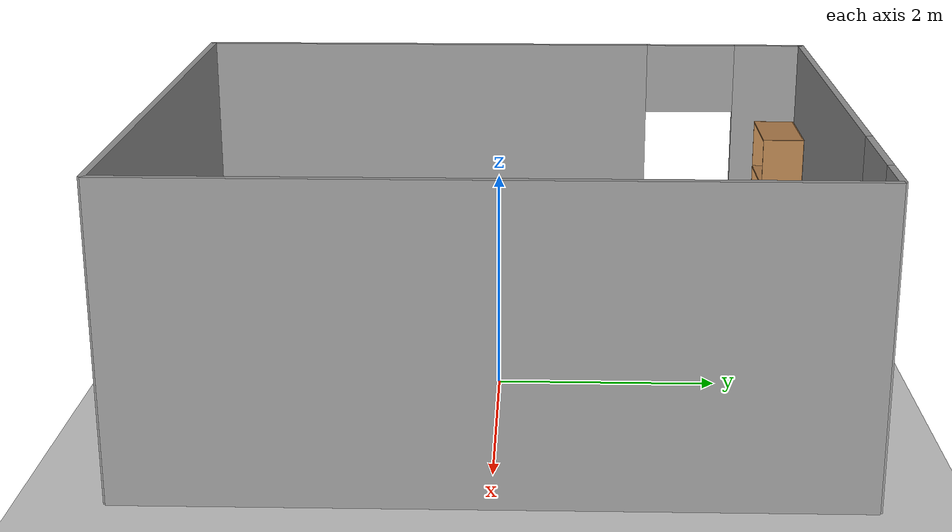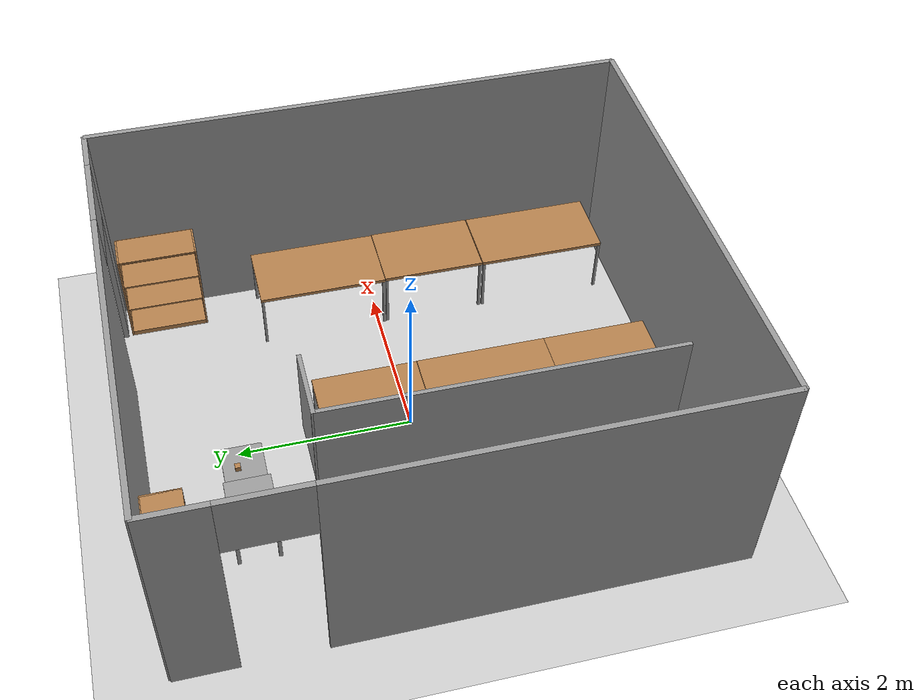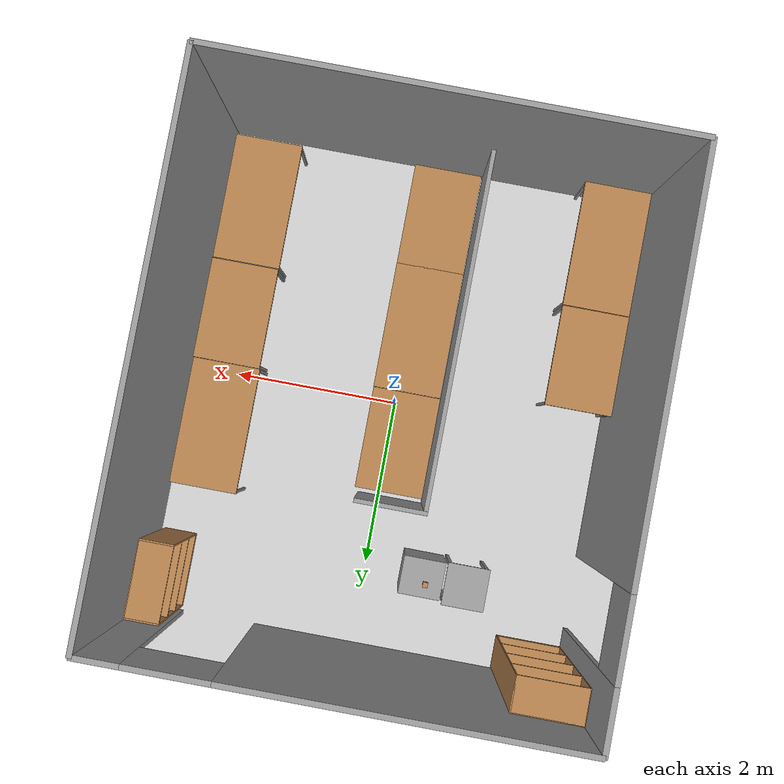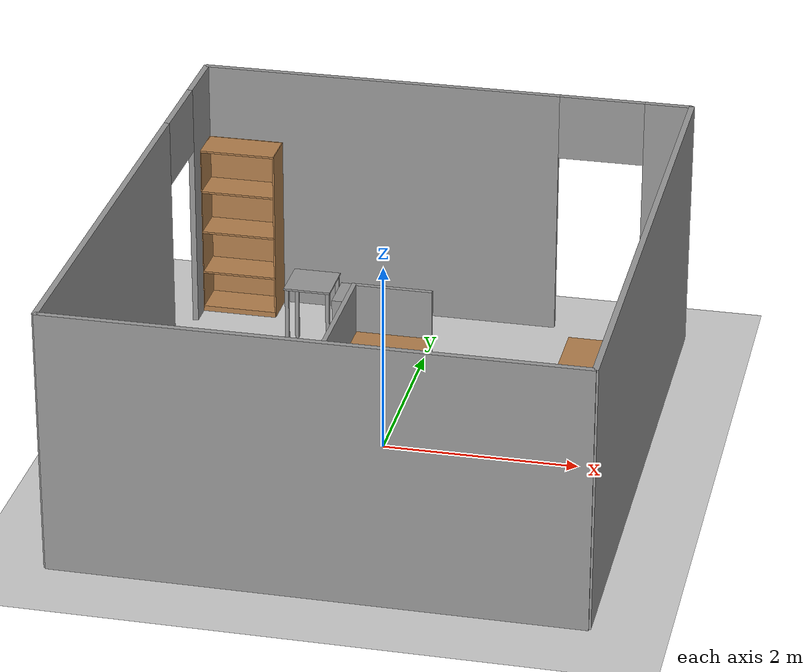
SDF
<sdf version="1.7">
 <world name="default">
  <light name="sun" type="directional">
   <pose>0 0 10 0 -0 0</pose>
   <diffuse>0.8 0.8 0.8 1</diffuse>
   <specular>0.2 0.2 0.2 1</specular>
   <attenuation>
    <range>1000</range>
    <constant>0.9</constant>
    <linear>0.01</linear>
    <quadratic>0.001</quadratic>
   </attenuation>
   <direction>-0.5 0.1 -0.9</direction>
   <spot><inner_angle>0</inner_angle><outer_angle>0</outer_angle><falloff>0</falloff></spot>
  </light>
  <model name="ground_plane">
   <static>1</static>
   <link name="link">
    <collision name="collision">
     <geometry><plane><normal>0 0 1</normal><size>100 100</size></plane></geometry>
     <surface>
      <contact><collide_bitmask>65535</collide_bitmask></contact>
      <friction><ode><mu>100</mu><mu2>50</mu2></ode></friction>
     </surface>
    </collision>
    <visual name="visual">
     <cast_shadows>0</cast_shadows>
     <geometry><plane><normal>0 0 1</normal><size>100 100</size></plane></geometry>
     <material>
      <script><uri>file://media/materials/scripts/gazebo.material</uri><name>Gazebo/Grey</name></script>
     </material>
    </visual>
   </link>
  </model>
  <gravity>0 0 -9.8</gravity>
  <magnetic_field>6e-06 2.3e-05 -4.2e-05</magnetic_field>
  <atmosphere type="adiabatic"/>
  <physics type="ode">
   <max_step_size>0.001</max_step_size>
   <real_time_factor>1</real_time_factor>
   <real_time_update_rate>1000</real_time_update_rate>
  </physics>
  <scene><ambient>0.4 0.4 0.4 1</ambient><background>0.7 0.7 0.7 1</background><shadows>1</shadows></scene>
  <spherical_coordinates>
   <surface_model>EARTH_WGS84</surface_model>
   <latitude_deg>0</latitude_deg>
   <longitude_deg>0</longitude_deg>
   <elevation>0</elevation>
   <heading_deg>0</heading_deg>
  </spherical_coordinates>
  <model name="bookshelf_0">
   <static>1</static>
   <link name="link">
    <inertial><mass>1</mass></inertial>
    <collision name="back">
     <pose>0 0.005 0.6 0 -0 0</pose>
     <geometry><box><size>0.9 0.01 1.2</size></box></geometry>
    </collision>
    <visual name="visual1">
     <pose>0 0.005 0.6 0 -0 0</pose>
     <geometry><box><size>0.9 0.01 1.2</size></box></geometry>
     <material>
      <script><uri>file://media/materials/scripts/gazebo.material</uri><name>Gazebo/Wood</name></script>
     </material>
    </visual>
    <collision name="left_side">
     <pose>0.45 -0.195 0.6 0 -0 0</pose>
     <geometry><box><size>0.02 0.4 1.2</size></box></geometry>
    </collision>
    <visual name="visual2">
     <pose>0.45 -0.195 0.6 0 -0 0</pose>
     <geometry><box><size>0.02 0.4 1.2</size></box></geometry>
     <material>
      <script><uri>file://media/materials/scripts/gazebo.material</uri><name>Gazebo/Wood</name></script>
     </material>
    </visual>
    <collision name="right_side">
     <pose>-0.45 -0.195 0.6 0 -0 0</pose>
     <geometry><box><size>0.02 0.4 1.2</size></box></geometry>
    </collision>
    <visual name="visual3">
     <pose>-0.45 -0.195 0.6 0 -0 0</pose>
     <geometry><box><size>0.02 0.4 1.2</size></box></geometry>
     <material>
      <script><uri>file://media/materials/scripts/gazebo.material</uri><name>Gazebo/Wood</name></script>
     </material>
    </visual>
    <collision name="bottom">
     <pose>0 -0.195 0.03 0 -0 0</pose>
     <geometry><box><size>0.88 0.4 0.06</size></box></geometry>
    </collision>
    <visual name="visual4">
     <pose>0 -0.195 0.03 0 -0 0</pose>
     <geometry><box><size>0.88 0.4 0.06</size></box></geometry>
     <material>
      <script><uri>file://media/materials/scripts/gazebo.material</uri><name>Gazebo/Wood</name></script>
     </material>
    </visual>
    <collision name="top">
     <pose>0 -0.195 1.19 0 -0 0</pose>
     <geometry><box><size>0.88 0.4 0.02</size></box></geometry>
    </collision>
    <visual name="visual5">
     <pose>0 -0.195 1.19 0 -0 0</pose>
     <geometry><box><size>0.88 0.4 0.02</size></box></geometry>
     <material>
      <script><uri>file://media/materials/scripts/gazebo.material</uri><name>Gazebo/Wood</name></script>
     </material>
    </visual>
    <collision name="low_shelf">
     <pose>0 -0.195 0.43 0 -0 0</pose>
     <geometry><box><size>0.88 0.4 0.02</size></box></geometry>
    </collision>
    <visual name="visual6">
     <pose>0 -0.195 0.43 0 -0 0</pose>
     <geometry><box><size>0.88 0.4 0.02</size></box></geometry>
     <material>
      <script><uri>file://media/materials/scripts/gazebo.material</uri><name>Gazebo/Wood</name></script>
     </material>
    </visual>
    <collision name="high_shelf">
     <pose>0 -0.195 0.8 0 -0 0</pose>
     <geometry><box><size>0.88 0.4 0.02</size></box></geometry>
    </collision>
    <visual name="visual7">
     <pose>0 -0.195 0.8 0 -0 0</pose>
     <geometry><box><size>0.88 0.4 0.02</size></box></geometry>
     <material>
      <script><uri>file://media/materials/scripts/gazebo.material</uri><name>Gazebo/Wood</name></script>
     </material>
    </visual>
   </link>
   <pose>2.53377 2.51385 0 0 0 -1.57235</pose>
  </model>
  <model name="IRAC">
   <link name="Wall_0">
    <pose>-2.61 0.007537 0 0 -0 1.5708</pose>
    <inertial>
     <mass>1</mass>
     <inertia><ixx>1</ixx><ixy>0</ixy><ixz>0</ixz><iyy>1</iyy><iyz>0</iyz><izz>1</izz></inertia>
    </inertial>
    <visual name="Wall_0_Visual_0">
     <pose>-0.79786 0 1.35 0 -0 0</pose>
     <geometry><box><size>4.52428 0.06 2.7</size></box></geometry>
     <material>
      <script><uri>file://media/materials/scripts/gazebo.material</uri><name>Gazebo/Grey</name></script>
      <ambient>1 1 1 1</ambient>
      <diffuse>0.7 0.7 0.7 1</diffuse>
      <specular>0.01 0.01 0.01 1</specular>
      <emissive>0 0 0 1</emissive>
     </material>
    </visual>
    <visual name="Wall_0_Visual_1">
     <pose>2.71214 0 1.35 0 -0 0</pose>
     <geometry><box><size>0.695721 0.06 2.7</size></box></geometry>
     <material>
      <script><uri>file://media/materials/scripts/gazebo.material</uri><name>Gazebo/Grey</name></script>
      <ambient>1 1 1 1</ambient>
      <diffuse>0.7 0.7 0.7 1</diffuse>
      <specular>0.01 0.01 0.01 1</specular>
      <emissive>0 0 0 1</emissive>
     </material>
    </visual>
    <visual name="Wall_0_Visual_2">
     <pose>1.91428 0 2.35 0 -0 0</pose>
     <geometry><box><size>0.9 0.06 0.7</size></box></geometry>
     <material>
      <script><uri>file://media/materials/scripts/gazebo.material</uri><name>Gazebo/Grey</name></script>
      <ambient>1 1 1 1</ambient>
      <diffuse>0.7 0.7 0.7 1</diffuse>
      <specular>0.01 0.01 0.01 1</specular>
      <emissive>0 0 0 1</emissive>
     </material>
    </visual>
    <collision name="Wall_0_Collision_0">
     <pose>-0.79786 0 1.35 0 -0 0</pose>
     <geometry><box><size>4.52428 0.06 2.7</size></box></geometry>
     <surface>
      <friction>
       <ode><mu>1</mu><mu2>1</mu2><fdir1>0 0 0</fdir1><slip1>0</slip1><slip2>0</slip2></ode>
       <torsional>
        <coefficient>1</coefficient>
        <patch_radius>0</patch_radius>
        <surface_radius>0</surface_radius>
        <use_patch_radius>1</use_patch_radius>
        <ode><slip>0</slip></ode>
       </torsional>
      </friction>
      <bounce><restitution_coefficient>0</restitution_coefficient><threshold>1e+06</threshold></bounce>
      <contact>
       <collide_without_contact>0</collide_without_contact>
       <collide_without_contact_bitmask>1</collide_without_contact_bitmask>
       <collide_bitmask>1</collide_bitmask>
       <ode>
        <soft_cfm>0</soft_cfm>
        <soft_erp>0.2</soft_erp>
        <kp>1e+13</kp>
        <kd>1</kd>
        <max_vel>0.01</max_vel>
        <min_depth>0</min_depth>
       </ode>
      </contact>
     </surface>
    </collision>
    <collision name="Wall_0_Collision_2">
     <pose>1.91428 0 2.35 0 -0 0</pose>
     <geometry><box><size>0.9 0.06 0.7</size></box></geometry>
     <surface>
      <friction>
       <ode><mu>1</mu><mu2>1</mu2><fdir1>0 0 0</fdir1><slip1>0</slip1><slip2>0</slip2></ode>
       <torsional>
        <coefficient>1</coefficient>
        <patch_radius>0</patch_radius>
        <surface_radius>0</surface_radius>
        <use_patch_radius>1</use_patch_radius>
        <ode><slip>0</slip></ode>
       </torsional>
      </friction>
      <bounce><restitution_coefficient>0</restitution_coefficient><threshold>1e+06</threshold></bounce>
      <contact>
       <collide_without_contact>0</collide_without_contact>
       <collide_without_contact_bitmask>1</collide_without_contact_bitmask>
       <collide_bitmask>1</collide_bitmask>
       <ode>
        <soft_cfm>0</soft_cfm>
        <soft_erp>0.2</soft_erp>
        <kp>1e+13</kp>
        <kd>1</kd>
        <max_vel>0.01</max_vel>
        <min_depth>0</min_depth>
       </ode>
      </contact>
     </surface>
    </collision>
    <collision name="Wall_0_Collision_1">
     <pose>2.71214 0 1.35 0 -0 0</pose>
     <geometry><box><size>0.695721 0.06 2.7</size></box></geometry>
     <surface>
      <friction>
       <ode><mu>1</mu><mu2>1</mu2><fdir1>0 0 0</fdir1><slip1>0</slip1><slip2>0</slip2></ode>
       <torsional>
        <coefficient>1</coefficient>
        <patch_radius>0</patch_radius>
        <surface_radius>0</surface_radius>
        <use_patch_radius>1</use_patch_radius>
        <ode><slip>0</slip></ode>
       </torsional>
      </friction>
      <bounce><restitution_coefficient>0</restitution_coefficient><threshold>1e+06</threshold></bounce>
      <contact>
       <collide_without_contact>0</collide_without_contact>
       <collide_without_contact_bitmask>1</collide_without_contact_bitmask>
       <collide_bitmask>1</collide_bitmask>
       <ode>
        <soft_cfm>0</soft_cfm>
        <soft_erp>0.2</soft_erp>
        <kp>1e+13</kp>
        <kd>1</kd>
        <max_vel>0.01</max_vel>
        <min_depth>0</min_depth>
       </ode>
      </contact>
     </surface>
    </collision>
   </link>
   <link name="Wall_11">
    <pose>-0.5825 -0.922463 0 0 -0 1.56726</pose>
    <visual name="Wall_11_Visual">
     <pose>0 0 0.6 0 -0 0</pose>
     <geometry><box><size>4.29 0.05 1.2</size></box></geometry>
     <material>
      <script><uri>file://media/materials/scripts/gazebo.material</uri><name>Gazebo/Grey</name></script>
      <ambient>1 1 1 1</ambient>
     </material>
    </visual>
    <collision name="Wall_11_Collision">
     <pose>0 0 0.6 0 -0 0</pose>
     <geometry><box><size>4.29 0.05 1.2</size></box></geometry>
     <surface>
      <friction>
       <ode><mu>1</mu><mu2>1</mu2><fdir1>0 0 0</fdir1><slip1>0</slip1><slip2>0</slip2></ode>
       <torsional>
        <coefficient>1</coefficient>
        <patch_radius>0</patch_radius>
        <surface_radius>0</surface_radius>
        <use_patch_radius>1</use_patch_radius>
        <ode><slip>0</slip></ode>
       </torsional>
      </friction>
      <bounce><restitution_coefficient>0</restitution_coefficient><threshold>1e+06</threshold></bounce>
      <contact>
       <collide_without_contact>0</collide_without_contact>
       <collide_without_contact_bitmask>1</collide_without_contact_bitmask>
       <collide_bitmask>1</collide_bitmask>
       <ode>
        <soft_cfm>0</soft_cfm>
        <soft_erp>0.2</soft_erp>
        <kp>1e+13</kp>
        <kd>1</kd>
        <max_vel>0.01</max_vel>
        <min_depth>0</min_depth>
       </ode>
      </contact>
     </surface>
    </collision>
   </link>
   <link name="Wall_13">
    <pose>-0.175 1.19754 0 0 -0 0</pose>
    <visual name="Wall_13_Visual">
     <pose>0 0 0.6 0 -0 0</pose>
     <geometry><box><size>0.85 0.05 1.2</size></box></geometry>
     <material>
      <script><uri>file://media/materials/scripts/gazebo.material</uri><name>Gazebo/Grey</name></script>
      <ambient>1 1 1 1</ambient>
     </material>
    </visual>
    <collision name="Wall_13_Collision">
     <pose>0 0 0.6 0 -0 0</pose>
     <geometry><box><size>0.85 0.05 1.2</size></box></geometry>
     <surface>
      <friction>
       <ode><mu>1</mu><mu2>1</mu2><fdir1>0 0 0</fdir1><slip1>0</slip1><slip2>0</slip2></ode>
       <torsional>
        <coefficient>1</coefficient>
        <patch_radius>0</patch_radius>
        <surface_radius>0</surface_radius>
        <use_patch_radius>1</use_patch_radius>
        <ode><slip>0</slip></ode>
       </torsional>
      </friction>
      <bounce><restitution_coefficient>0</restitution_coefficient><threshold>1e+06</threshold></bounce>
      <contact>
       <collide_without_contact>0</collide_without_contact>
       <collide_without_contact_bitmask>1</collide_without_contact_bitmask>
       <collide_bitmask>1</collide_bitmask>
       <ode>
        <soft_cfm>0</soft_cfm>
        <soft_erp>0.2</soft_erp>
        <kp>1e+13</kp>
        <kd>1</kd>
        <max_vel>0.01</max_vel>
        <min_depth>0</min_depth>
       </ode>
      </contact>
     </surface>
    </collision>
   </link>
   <link name="Wall_2">
    <pose>0 -3.04246 0 0 -0 0</pose>
    <inertial>
     <mass>1</mass>
     <inertia><ixx>1</ixx><ixy>0</ixy><ixz>0</ixz><iyy>1</iyy><iyz>0</iyz><izz>1</izz></inertia>
    </inertial>
    <visual name="Wall_2_Visual">
     <pose>0 0 1.35 0 -0 0</pose>
     <geometry><box><size>5.24 0.06 2.7</size></box></geometry>
     <material>
      <script><uri>file://media/materials/scripts/gazebo.material</uri><name>Gazebo/Grey</name></script>
      <ambient>1 1 1 1</ambient>
      <diffuse>0.7 0.7 0.7 1</diffuse>
      <specular>0.01 0.01 0.01 1</specular>
      <emissive>0 0 0 1</emissive>
     </material>
    </visual>
    <collision name="Wall_2_Collision">
     <pose>0 0 1.35 0 -0 0</pose>
     <geometry><box><size>5.24 0.06 2.7</size></box></geometry>
     <surface>
      <friction>
       <ode><mu>1</mu><mu2>1</mu2><fdir1>0 0 0</fdir1><slip1>0</slip1><slip2>0</slip2></ode>
       <torsional>
        <coefficient>1</coefficient>
        <patch_radius>0</patch_radius>
        <surface_radius>0</surface_radius>
        <use_patch_radius>1</use_patch_radius>
        <ode><slip>0</slip></ode>
       </torsional>
      </friction>
      <bounce><restitution_coefficient>0</restitution_coefficient><threshold>1e+06</threshold></bounce>
      <contact>
       <collide_without_contact>0</collide_without_contact>
       <collide_without_contact_bitmask>1</collide_without_contact_bitmask>
       <collide_bitmask>1</collide_bitmask>
       <ode>
        <soft_cfm>0</soft_cfm>
        <soft_erp>0.2</soft_erp>
        <kp>1e+13</kp>
        <kd>1</kd>
        <max_vel>0.01</max_vel>
        <min_depth>0</min_depth>
       </ode>
      </contact>
     </surface>
    </collision>
   </link>
   <link name="Wall_4">
    <pose>2.61 0.007537 0 0 -0 1.5708</pose>
    <inertial>
     <mass>1</mass>
     <inertia><ixx>1</ixx><ixy>0</ixy><ixz>0</ixz><iyy>1</iyy><iyz>0</iyz><izz>1</izz></inertia>
    </inertial>
    <visual name="Wall_4_Visual">
     <pose>0 0 1.35 0 -0 0</pose>
     <geometry><box><size>6.12 0.06 2.7</size></box></geometry>
     <material>
      <script><uri>file://media/materials/scripts/gazebo.material</uri><name>Gazebo/Grey</name></script>
      <ambient>1 1 1 1</ambient>
      <diffuse>0.7 0.7 0.7 1</diffuse>
      <specular>0.01 0.01 0.01 1</specular>
      <emissive>0 0 0 1</emissive>
     </material>
    </visual>
    <collision name="Wall_4_Collision">
     <pose>0 0 1.35 0 -0 0</pose>
     <geometry><box><size>6.12 0.06 2.7</size></box></geometry>
     <surface>
      <friction>
       <ode><mu>1</mu><mu2>1</mu2><fdir1>0 0 0</fdir1><slip1>0</slip1><slip2>0</slip2></ode>
       <torsional>
        <coefficient>1</coefficient>
        <patch_radius>0</patch_radius>
        <surface_radius>0</surface_radius>
        <use_patch_radius>1</use_patch_radius>
        <ode><slip>0</slip></ode>
       </torsional>
      </friction>
      <bounce><restitution_coefficient>0</restitution_coefficient><threshold>1e+06</threshold></bounce>
      <contact>
       <collide_without_contact>0</collide_without_contact>
       <collide_without_contact_bitmask>1</collide_without_contact_bitmask>
       <collide_bitmask>1</collide_bitmask>
       <ode>
        <soft_cfm>0</soft_cfm>
        <soft_erp>0.2</soft_erp>
        <kp>1e+13</kp>
        <kd>1</kd>
        <max_vel>0.01</max_vel>
        <min_depth>0</min_depth>
       </ode>
      </contact>
     </surface>
    </collision>
   </link>
   <link name="Wall_9">
    <pose>0 3.05754 0 0 -0 0</pose>
    <inertial>
     <mass>1</mass>
     <inertia><ixx>1</ixx><ixy>0</ixy><ixz>0</ixz><iyy>1</iyy><iyz>0</iyz><izz>1</izz></inertia>
    </inertial>
    <visual name="Wall_9_Visual_0">
     <pose>-0.699649 0 1.35 0 -0 0</pose>
     <geometry><box><size>3.8407 0.06 2.7</size></box></geometry>
     <material>
      <script><uri>file://media/materials/scripts/gazebo.material</uri><name>Gazebo/Grey</name></script>
      <ambient>1 1 1 1</ambient>
      <diffuse>0.7 0.7 0.7 1</diffuse>
      <specular>0.01 0.01 0.01 1</specular>
      <emissive>0 0 0 1</emissive>
     </material>
    </visual>
    <visual name="Wall_9_Visual_1">
     <pose>2.37035 0 1.35 0 -0 0</pose>
     <geometry><box><size>0.499297 0.06 2.7</size></box></geometry>
     <material>
      <script><uri>file://media/materials/scripts/gazebo.material</uri><name>Gazebo/Grey</name></script>
      <ambient>1 1 1 1</ambient>
      <diffuse>0.7 0.7 0.7 1</diffuse>
      <specular>0.01 0.01 0.01 1</specular>
      <emissive>0 0 0 1</emissive>
     </material>
    </visual>
    <visual name="Wall_9_Visual_2">
     <pose>1.6707 0 2.35 0 -0 0</pose>
     <geometry><box><size>0.9 0.06 0.7</size></box></geometry>
     <material>
      <script><uri>file://media/materials/scripts/gazebo.material</uri><name>Gazebo/Grey</name></script>
      <ambient>1 1 1 1</ambient>
      <diffuse>0.7 0.7 0.7 1</diffuse>
      <specular>0.01 0.01 0.01 1</specular>
      <emissive>0 0 0 1</emissive>
     </material>
    </visual>
    <collision name="Wall_9_Collision_0">
     <pose>-0.699649 0 1.35 0 -0 0</pose>
     <geometry><box><size>3.8407 0.06 2.7</size></box></geometry>
     <surface>
      <friction>
       <ode><mu>1</mu><mu2>1</mu2><fdir1>0 0 0</fdir1><slip1>0</slip1><slip2>0</slip2></ode>
       <torsional>
        <coefficient>1</coefficient>
        <patch_radius>0</patch_radius>
        <surface_radius>0</surface_radius>
        <use_patch_radius>1</use_patch_radius>
        <ode><slip>0</slip></ode>
       </torsional>
      </friction>
      <bounce><restitution_coefficient>0</restitution_coefficient><threshold>1e+06</threshold></bounce>
      <contact>
       <collide_without_contact>0</collide_without_contact>
       <collide_without_contact_bitmask>1</collide_without_contact_bitmask>
       <collide_bitmask>1</collide_bitmask>
       <ode>
        <soft_cfm>0</soft_cfm>
        <soft_erp>0.2</soft_erp>
        <kp>1e+13</kp>
        <kd>1</kd>
        <max_vel>0.01</max_vel>
        <min_depth>0</min_depth>
       </ode>
      </contact>
     </surface>
    </collision>
    <collision name="Wall_9_Collision_1">
     <pose>2.37035 0 1.35 0 -0 0</pose>
     <geometry><box><size>0.499297 0.06 2.7</size></box></geometry>
     <surface>
      <friction>
       <ode><mu>1</mu><mu2>1</mu2><fdir1>0 0 0</fdir1><slip1>0</slip1><slip2>0</slip2></ode>
       <torsional>
        <coefficient>1</coefficient>
        <patch_radius>0</patch_radius>
        <surface_radius>0</surface_radius>
        <use_patch_radius>1</use_patch_radius>
        <ode><slip>0</slip></ode>
       </torsional>
      </friction>
      <bounce><restitution_coefficient>0</restitution_coefficient><threshold>1e+06</threshold></bounce>
      <contact>
       <collide_without_contact>0</collide_without_contact>
       <collide_without_contact_bitmask>1</collide_without_contact_bitmask>
       <collide_bitmask>1</collide_bitmask>
       <ode>
        <soft_cfm>0</soft_cfm>
        <soft_erp>0.2</soft_erp>
        <kp>1e+13</kp>
        <kd>1</kd>
        <max_vel>0.01</max_vel>
        <min_depth>0</min_depth>
       </ode>
      </contact>
     </surface>
    </collision>
    <collision name="Wall_9_Collision_2">
     <pose>1.6707 0 2.35 0 -0 0</pose>
     <geometry><box><size>0.9 0.06 0.7</size></box></geometry>
     <surface>
      <friction>
       <ode><mu>1</mu><mu2>1</mu2><fdir1>0 0 0</fdir1><slip1>0</slip1><slip2>0</slip2></ode>
       <torsional>
        <coefficient>1</coefficient>
        <patch_radius>0</patch_radius>
        <surface_radius>0</surface_radius>
        <use_patch_radius>1</use_patch_radius>
        <ode><slip>0</slip></ode>
       </torsional>
      </friction>
      <bounce><restitution_coefficient>0</restitution_coefficient><threshold>1e+06</threshold></bounce>
      <contact>
       <collide_without_contact>0</collide_without_contact>
       <collide_without_contact_bitmask>1</collide_without_contact_bitmask>
       <collide_bitmask>1</collide_bitmask>
       <ode>
        <soft_cfm>0</soft_cfm>
        <soft_erp>0.2</soft_erp>
        <kp>1e+13</kp>
        <kd>1</kd>
        <max_vel>0.01</max_vel>
        <min_depth>0</min_depth>
       </ode>
      </contact>
     </surface>
    </collision>
   </link>
   <static>1</static>
   <pose>0 -0.007537 0 0 -0 0</pose>
  </model>
  <model name="table_long">
   <link name="link">
    <inertial>
     <mass>1</mass>
     <inertia><ixx>1</ixx><ixy>0</ixy><ixz>0</ixz><iyy>1</iyy><iyz>0</iyz><izz>1</izz></inertia>
    </inertial>
    <visual name="front_left_leg">
     <pose>0.73 0.38 0.35 0 -0 0</pose>
     <geometry><box><size>0.03 0.03 0.7</size></box></geometry>
     <material>
      <script><uri>file://media/materials/scripts/gazebo.material</uri><name>Gazebo/Grey</name></script>
      <ambient>0.3 0.3 0.3 1</ambient>
      <diffuse>0.7 0.7 0.7 1</diffuse>
      <specular>0.01 0.01 0.01 1</specular>
      <emissive>0 0 0 1</emissive>
     </material>
    </visual>
    <visual name="front_right_leg">
     <pose>0.73 -0.38 0.35 0 -0 0</pose>
     <geometry><box><size>0.03 0.03 0.7</size></box></geometry>
     <material>
      <script><uri>file://media/materials/scripts/gazebo.material</uri><name>Gazebo/Grey</name></script>
      <ambient>0.3 0.3 0.3 1</ambient>
      <diffuse>0.7 0.7 0.7 1</diffuse>
      <specular>0.01 0.01 0.01 1</specular>
      <emissive>0 0 0 1</emissive>
     </material>
    </visual>
    <visual name="visual1">
     <pose>0 0 0.7 0 -0 0</pose>
     <geometry><box><size>1.5 0.8 0.04</size></box></geometry>
     <material>
      <script><uri>file://media/materials/scripts/gazebo.material</uri><name>Gazebo/Wood</name></script>
      <ambient>1 1 1 1</ambient>
      <diffuse>1 1 1 1</diffuse>
      <specular>0.2 0.2 0.2 1</specular>
      <emissive>0 0 0 1</emissive>
     </material>
    </visual>
    <visual name="back_right_leg">
     <pose>-0.73 -0.38 0.35 0 -0 0</pose>
     <geometry><box><size>0.03 0.03 0.7</size></box></geometry>
     <material>
      <script><uri>file://media/materials/scripts/gazebo.material</uri><name>Gazebo/Grey</name></script>
      <ambient>0.3 0.3 0.3 1</ambient>
      <diffuse>0.7 0.7 0.7 1</diffuse>
      <specular>0.01 0.01 0.01 1</specular>
      <emissive>0 0 0 1</emissive>
     </material>
    </visual>
    <visual name="back_left_leg">
     <pose>-0.73 0.38 0.35 0 -0 0</pose>
     <geometry><box><size>0.03 0.03 0.7</size></box></geometry>
     <material>
      <script><uri>file://media/materials/scripts/gazebo.material</uri><name>Gazebo/Grey</name></script>
      <ambient>0.3 0.3 0.3 1</ambient>
      <diffuse>0.7 0.7 0.7 1</diffuse>
      <specular>0.01 0.01 0.01 1</specular>
      <emissive>0 0 0 1</emissive>
     </material>
    </visual>
    <collision name="front_right_leg">
     <pose>0.73 -0.38 0.35 0 -0 0</pose>
     <geometry><box><size>0.03 0.03 0.7</size></box></geometry>
     <surface>
      <friction>
       <ode><mu>1</mu><mu2>1</mu2><fdir1>0 0 0</fdir1><slip1>0</slip1><slip2>0</slip2></ode>
       <torsional>
        <coefficient>1</coefficient>
        <patch_radius>0</patch_radius>
        <surface_radius>0</surface_radius>
        <use_patch_radius>1</use_patch_radius>
        <ode><slip>0</slip></ode>
       </torsional>
      </friction>
      <bounce><restitution_coefficient>0</restitution_coefficient><threshold>1e+06</threshold></bounce>
      <contact>
       <collide_without_contact>0</collide_without_contact>
       <collide_without_contact_bitmask>1</collide_without_contact_bitmask>
       <collide_bitmask>1</collide_bitmask>
       <ode>
        <soft_cfm>0</soft_cfm>
        <soft_erp>0.2</soft_erp>
        <kp>1e+13</kp>
        <kd>1</kd>
        <max_vel>0.01</max_vel>
        <min_depth>0</min_depth>
       </ode>
      </contact>
     </surface>
    </collision>
    <collision name="front_left_leg">
     <pose>0.73 0.38 0.35 0 -0 0</pose>
     <geometry><box><size>0.03 0.03 0.699999</size></box></geometry>
     <surface>
      <friction>
       <ode><mu>1</mu><mu2>1</mu2><fdir1>0 0 0</fdir1><slip1>0</slip1><slip2>0</slip2></ode>
       <torsional>
        <coefficient>1</coefficient>
        <patch_radius>0</patch_radius>
        <surface_radius>0</surface_radius>
        <use_patch_radius>1</use_patch_radius>
        <ode><slip>0</slip></ode>
       </torsional>
      </friction>
      <bounce><restitution_coefficient>0</restitution_coefficient><threshold>1e+06</threshold></bounce>
      <contact>
       <collide_without_contact>0</collide_without_contact>
       <collide_without_contact_bitmask>1</collide_without_contact_bitmask>
       <collide_bitmask>1</collide_bitmask>
       <ode>
        <soft_cfm>0</soft_cfm>
        <soft_erp>0.2</soft_erp>
        <kp>1e+13</kp>
        <kd>1</kd>
        <max_vel>0.01</max_vel>
        <min_depth>0</min_depth>
       </ode>
      </contact>
     </surface>
    </collision>
    <collision name="back_right_leg">
     <pose>-0.73 -0.38 0.35 0 -0 0</pose>
     <geometry><box><size>0.03 0.03 0.7</size></box></geometry>
     <surface>
      <friction>
       <ode><mu>1</mu><mu2>1</mu2><fdir1>0 0 0</fdir1><slip1>0</slip1><slip2>0</slip2></ode>
       <torsional>
        <coefficient>1</coefficient>
        <patch_radius>0</patch_radius>
        <surface_radius>0</surface_radius>
        <use_patch_radius>1</use_patch_radius>
        <ode><slip>0</slip></ode>
       </torsional>
      </friction>
      <bounce><restitution_coefficient>0</restitution_coefficient><threshold>1e+06</threshold></bounce>
      <contact>
       <collide_without_contact>0</collide_without_contact>
       <collide_without_contact_bitmask>1</collide_without_contact_bitmask>
       <collide_bitmask>1</collide_bitmask>
       <ode>
        <soft_cfm>0</soft_cfm>
        <soft_erp>0.2</soft_erp>
        <kp>1e+13</kp>
        <kd>1</kd>
        <max_vel>0.01</max_vel>
        <min_depth>0</min_depth>
       </ode>
      </contact>
     </surface>
    </collision>
    <collision name="surface">
     <pose>0 0 0.7 0 -0 0</pose>
     <geometry><box><size>1.5 0.8 0.04</size></box></geometry>
     <surface>
      <friction>
       <ode><mu>0.6</mu><mu2>0.6</mu2><fdir1>0 0 0</fdir1><slip1>0</slip1><slip2>0</slip2></ode>
       <torsional>
        <coefficient>1</coefficient>
        <patch_radius>0</patch_radius>
        <surface_radius>0</surface_radius>
        <use_patch_radius>1</use_patch_radius>
        <ode><slip>0</slip></ode>
       </torsional>
      </friction>
      <bounce><restitution_coefficient>0</restitution_coefficient><threshold>1e+06</threshold></bounce>
      <contact>
       <collide_without_contact>0</collide_without_contact>
       <collide_without_contact_bitmask>1</collide_without_contact_bitmask>
       <collide_bitmask>1</collide_bitmask>
       <ode>
        <soft_cfm>0</soft_cfm>
        <soft_erp>0.2</soft_erp>
        <kp>1e+13</kp>
        <kd>1</kd>
        <max_vel>0.01</max_vel>
        <min_depth>0</min_depth>
       </ode>
      </contact>
     </surface>
    </collision>
    <collision name="back_left_leg">
     <pose>-0.73 0.38 0.35 0 -0 0</pose>
     <geometry><box><size>0.03 0.03 0.7</size></box></geometry>
     <surface>
      <friction>
       <ode><mu>1</mu><mu2>1</mu2><fdir1>0 0 0</fdir1><slip1>0</slip1><slip2>0</slip2></ode>
       <torsional>
        <coefficient>1</coefficient>
        <patch_radius>0</patch_radius>
        <surface_radius>0</surface_radius>
        <use_patch_radius>1</use_patch_radius>
        <ode><slip>0</slip></ode>
       </torsional>
      </friction>
      <bounce><restitution_coefficient>0</restitution_coefficient><threshold>1e+06</threshold></bounce>
      <contact>
       <collide_without_contact>0</collide_without_contact>
       <collide_without_contact_bitmask>1</collide_without_contact_bitmask>
       <collide_bitmask>1</collide_bitmask>
       <ode>
        <soft_cfm>0</soft_cfm>
        <soft_erp>0.2</soft_erp>
        <kp>1e+13</kp>
        <kd>1</kd>
        <max_vel>0.01</max_vel>
        <min_depth>0</min_depth>
       </ode>
      </contact>
     </surface>
    </collision>
   </link>
   <static>1</static>
   <pose>-2.15133 -2.25174 0 0 0 -1.5749</pose>
  </model>
  <model name="table_long_clone">
   <link name="link">
    <inertial>
     <mass>1</mass>
     <inertia><ixx>1</ixx><ixy>0</ixy><ixz>0</ixz><iyy>1</iyy><iyz>0</iyz><izz>1</izz></inertia>
    </inertial>
    <visual name="front_left_leg">
     <pose>0.73 0.38 0.35 0 -0 0</pose>
     <geometry><box><size>0.03 0.03 0.7</size></box></geometry>
     <material>
      <script><uri>file://media/materials/scripts/gazebo.material</uri><name>Gazebo/Grey</name></script>
      <ambient>0.3 0.3 0.3 1</ambient>
      <diffuse>0.7 0.7 0.7 1</diffuse>
      <specular>0.01 0.01 0.01 1</specular>
      <emissive>0 0 0 1</emissive>
     </material>
    </visual>
    <visual name="front_right_leg">
     <pose>0.73 -0.38 0.35 0 -0 0</pose>
     <geometry><box><size>0.03 0.03 0.7</size></box></geometry>
     <material>
      <script><uri>file://media/materials/scripts/gazebo.material</uri><name>Gazebo/Grey</name></script>
      <ambient>0.3 0.3 0.3 1</ambient>
      <diffuse>0.7 0.7 0.7 1</diffuse>
      <specular>0.01 0.01 0.01 1</specular>
      <emissive>0 0 0 1</emissive>
     </material>
    </visual>
    <visual name="visual1">
     <pose>0 0 0.7 0 -0 0</pose>
     <geometry><box><size>1.5 0.8 0.04</size></box></geometry>
     <material>
      <script><uri>file://media/materials/scripts/gazebo.material</uri><name>Gazebo/Wood</name></script>
      <ambient>1 1 1 1</ambient>
      <diffuse>1 1 1 1</diffuse>
      <specular>0.2 0.2 0.2 1</specular>
      <emissive>0 0 0 1</emissive>
     </material>
    </visual>
    <visual name="back_right_leg">
     <pose>-0.73 -0.38 0.35 0 -0 0</pose>
     <geometry><box><size>0.03 0.03 0.7</size></box></geometry>
     <material>
      <script><uri>file://media/materials/scripts/gazebo.material</uri><name>Gazebo/Grey</name></script>
      <ambient>0.3 0.3 0.3 1</ambient>
      <diffuse>0.7 0.7 0.7 1</diffuse>
      <specular>0.01 0.01 0.01 1</specular>
      <emissive>0 0 0 1</emissive>
     </material>
    </visual>
    <visual name="back_left_leg">
     <pose>-0.73 0.38 0.35 0 -0 0</pose>
     <geometry><box><size>0.03 0.03 0.7</size></box></geometry>
     <material>
      <script><uri>file://media/materials/scripts/gazebo.material</uri><name>Gazebo/Grey</name></script>
      <ambient>0.3 0.3 0.3 1</ambient>
      <diffuse>0.7 0.7 0.7 1</diffuse>
      <specular>0.01 0.01 0.01 1</specular>
      <emissive>0 0 0 1</emissive>
     </material>
    </visual>
    <collision name="front_right_leg">
     <pose>0.73 -0.38 0.35 0 -0 0</pose>
     <geometry><box><size>0.03 0.03 0.7</size></box></geometry>
     <surface>
      <friction>
       <ode><mu>1</mu><mu2>1</mu2><fdir1>0 0 0</fdir1><slip1>0</slip1><slip2>0</slip2></ode>
       <torsional>
        <coefficient>1</coefficient>
        <patch_radius>0</patch_radius>
        <surface_radius>0</surface_radius>
        <use_patch_radius>1</use_patch_radius>
        <ode><slip>0</slip></ode>
       </torsional>
      </friction>
      <bounce><restitution_coefficient>0</restitution_coefficient><threshold>1e+06</threshold></bounce>
      <contact>
       <collide_without_contact>0</collide_without_contact>
       <collide_without_contact_bitmask>1</collide_without_contact_bitmask>
       <collide_bitmask>1</collide_bitmask>
       <ode>
        <soft_cfm>0</soft_cfm>
        <soft_erp>0.2</soft_erp>
        <kp>1e+13</kp>
        <kd>1</kd>
        <max_vel>0.01</max_vel>
        <min_depth>0</min_depth>
       </ode>
      </contact>
     </surface>
    </collision>
    <collision name="front_left_leg">
     <pose>0.73 0.38 0.35 0 -0 0</pose>
     <geometry><box><size>0.03 0.03 0.699999</size></box></geometry>
     <surface>
      <friction>
       <ode><mu>1</mu><mu2>1</mu2><fdir1>0 0 0</fdir1><slip1>0</slip1><slip2>0</slip2></ode>
       <torsional>
        <coefficient>1</coefficient>
        <patch_radius>0</patch_radius>
        <surface_radius>0</surface_radius>
        <use_patch_radius>1</use_patch_radius>
        <ode><slip>0</slip></ode>
       </torsional>
      </friction>
      <bounce><restitution_coefficient>0</restitution_coefficient><threshold>1e+06</threshold></bounce>
      <contact>
       <collide_without_contact>0</collide_without_contact>
       <collide_without_contact_bitmask>1</collide_without_contact_bitmask>
       <collide_bitmask>1</collide_bitmask>
       <ode>
        <soft_cfm>0</soft_cfm>
        <soft_erp>0.2</soft_erp>
        <kp>1e+13</kp>
        <kd>1</kd>
        <max_vel>0.01</max_vel>
        <min_depth>0</min_depth>
       </ode>
      </contact>
     </surface>
    </collision>
    <collision name="back_right_leg">
     <pose>-0.73 -0.38 0.35 0 -0 0</pose>
     <geometry><box><size>0.03 0.03 0.7</size></box></geometry>
     <surface>
      <friction>
       <ode><mu>1</mu><mu2>1</mu2><fdir1>0 0 0</fdir1><slip1>0</slip1><slip2>0</slip2></ode>
       <torsional>
        <coefficient>1</coefficient>
        <patch_radius>0</patch_radius>
        <surface_radius>0</surface_radius>
        <use_patch_radius>1</use_patch_radius>
        <ode><slip>0</slip></ode>
       </torsional>
      </friction>
      <bounce><restitution_coefficient>0</restitution_coefficient><threshold>1e+06</threshold></bounce>
      <contact>
       <collide_without_contact>0</collide_without_contact>
       <collide_without_contact_bitmask>1</collide_without_contact_bitmask>
       <collide_bitmask>1</collide_bitmask>
       <ode>
        <soft_cfm>0</soft_cfm>
        <soft_erp>0.2</soft_erp>
        <kp>1e+13</kp>
        <kd>1</kd>
        <max_vel>0.01</max_vel>
        <min_depth>0</min_depth>
       </ode>
      </contact>
     </surface>
    </collision>
    <collision name="surface">
     <pose>0 0 0.7 0 -0 0</pose>
     <geometry><box><size>1.5 0.8 0.04</size></box></geometry>
     <surface>
      <friction>
       <ode><mu>0.6</mu><mu2>0.6</mu2><fdir1>0 0 0</fdir1><slip1>0</slip1><slip2>0</slip2></ode>
       <torsional>
        <coefficient>1</coefficient>
        <patch_radius>0</patch_radius>
        <surface_radius>0</surface_radius>
        <use_patch_radius>1</use_patch_radius>
        <ode><slip>0</slip></ode>
       </torsional>
      </friction>
      <bounce><restitution_coefficient>0</restitution_coefficient><threshold>1e+06</threshold></bounce>
      <contact>
       <collide_without_contact>0</collide_without_contact>
       <collide_without_contact_bitmask>1</collide_without_contact_bitmask>
       <collide_bitmask>1</collide_bitmask>
       <ode>
        <soft_cfm>0</soft_cfm>
        <soft_erp>0.2</soft_erp>
        <kp>1e+13</kp>
        <kd>1</kd>
        <max_vel>0.01</max_vel>
        <min_depth>0</min_depth>
       </ode>
      </contact>
     </surface>
    </collision>
    <collision name="back_left_leg">
     <pose>-0.73 0.38 0.35 0 -0 0</pose>
     <geometry><box><size>0.03 0.03 0.7</size></box></geometry>
     <surface>
      <friction>
       <ode><mu>1</mu><mu2>1</mu2><fdir1>0 0 0</fdir1><slip1>0</slip1><slip2>0</slip2></ode>
       <torsional>
        <coefficient>1</coefficient>
        <patch_radius>0</patch_radius>
        <surface_radius>0</surface_radius>
        <use_patch_radius>1</use_patch_radius>
        <ode><slip>0</slip></ode>
       </torsional>
      </friction>
      <bounce><restitution_coefficient>0</restitution_coefficient><threshold>1e+06</threshold></bounce>
      <contact>
       <collide_without_contact>0</collide_without_contact>
       <collide_without_contact_bitmask>1</collide_without_contact_bitmask>
       <collide_bitmask>1</collide_bitmask>
       <ode>
        <soft_cfm>0</soft_cfm>
        <soft_erp>0.2</soft_erp>
        <kp>1e+13</kp>
        <kd>1</kd>
        <max_vel>0.01</max_vel>
        <min_depth>0</min_depth>
       </ode>
      </contact>
     </surface>
    </collision>
   </link>
   <static>1</static>
   <pose>-0.120005 -0.88588 0 0 -0 1.57</pose>
  </model>
  <model name="table_short_clone">
   <link name="link">
    <inertial>
     <mass>1</mass>
     <inertia><ixx>1</ixx><ixy>0</ixy><ixz>0</ixz><iyy>1</iyy><iyz>0</iyz><izz>1</izz></inertia>
    </inertial>
    <visual name="front_right_leg">
     <pose>0.58 -0.38 0.35 0 -0 0</pose>
     <geometry><box><size>0.03 0.03 0.7</size></box></geometry>
     <material>
      <script><uri>file://media/materials/scripts/gazebo.material</uri><name>Gazebo/Grey</name></script>
      <ambient>0.3 0.3 0.3 1</ambient>
      <diffuse>0.7 0.7 0.7 1</diffuse>
      <specular>0.01 0.01 0.01 1</specular>
      <emissive>0 0 0 1</emissive>
     </material>
    </visual>
    <visual name="back_left_leg">
     <pose>-0.58 0.38 0.35 0 -0 0</pose>
     <geometry><box><size>0.03 0.03 0.7</size></box></geometry>
     <material>
      <script><uri>file://media/materials/scripts/gazebo.material</uri><name>Gazebo/Grey</name></script>
      <ambient>0.3 0.3 0.3 1</ambient>
      <diffuse>0.7 0.7 0.7 1</diffuse>
      <specular>0.01 0.01 0.01 1</specular>
      <emissive>0 0 0 1</emissive>
     </material>
    </visual>
    <visual name="front_left_leg">
     <pose>0.58 0.38 0.35 0 -0 0</pose>
     <geometry><box><size>0.03 0.03 0.7</size></box></geometry>
     <material>
      <script><uri>file://media/materials/scripts/gazebo.material</uri><name>Gazebo/Grey</name></script>
      <ambient>0.3 0.3 0.3 1</ambient>
      <diffuse>0.7 0.7 0.7 1</diffuse>
      <specular>0.01 0.01 0.01 1</specular>
      <emissive>0 0 0 1</emissive>
     </material>
    </visual>
    <visual name="back_right_leg">
     <pose>-0.58 -0.38 0.35 0 -0 0</pose>
     <geometry><box><size>0.03 0.03 0.7</size></box></geometry>
     <material>
      <script><uri>file://media/materials/scripts/gazebo.material</uri><name>Gazebo/Grey</name></script>
      <ambient>0.3 0.3 0.3 1</ambient>
      <diffuse>0.7 0.7 0.7 1</diffuse>
      <specular>0.01 0.01 0.01 1</specular>
      <emissive>0 0 0 1</emissive>
     </material>
    </visual>
    <visual name="visual1">
     <pose>0 0 0.7 0 -0 0</pose>
     <geometry><box><size>1.2 0.8 0.04</size></box></geometry>
     <material>
      <script><uri>file://media/materials/scripts/gazebo.material</uri><name>Gazebo/Wood</name></script>
      <ambient>1 1 1 1</ambient>
      <diffuse>1 1 1 1</diffuse>
      <specular>0.2 0.2 0.2 1</specular>
      <emissive>0 0 0 1</emissive>
     </material>
    </visual>
    <collision name="front_right_leg">
     <pose>0.58 -0.38 0.35 0 -0 0</pose>
     <geometry><box><size>0.03 0.03 0.7</size></box></geometry>
     <surface>
      <friction>
       <ode><mu>1</mu><mu2>1</mu2><fdir1>0 0 0</fdir1><slip1>0</slip1><slip2>0</slip2></ode>
       <torsional>
        <coefficient>1</coefficient>
        <patch_radius>0</patch_radius>
        <surface_radius>0</surface_radius>
        <use_patch_radius>1</use_patch_radius>
        <ode><slip>0</slip></ode>
       </torsional>
      </friction>
      <bounce><restitution_coefficient>0</restitution_coefficient><threshold>1e+06</threshold></bounce>
      <contact>
       <collide_without_contact>0</collide_without_contact>
       <collide_without_contact_bitmask>1</collide_without_contact_bitmask>
       <collide_bitmask>1</collide_bitmask>
       <ode>
        <soft_cfm>0</soft_cfm>
        <soft_erp>0.2</soft_erp>
        <kp>1e+13</kp>
        <kd>1</kd>
        <max_vel>0.01</max_vel>
        <min_depth>0</min_depth>
       </ode>
      </contact>
     </surface>
    </collision>
    <collision name="back_left_leg">
     <pose>-0.58 0.38 0.35 0 -0 0</pose>
     <geometry><box><size>0.03 0.03 0.7</size></box></geometry>
     <surface>
      <friction>
       <ode><mu>1</mu><mu2>1</mu2><fdir1>0 0 0</fdir1><slip1>0</slip1><slip2>0</slip2></ode>
       <torsional>
        <coefficient>1</coefficient>
        <patch_radius>0</patch_radius>
        <surface_radius>0</surface_radius>
        <use_patch_radius>1</use_patch_radius>
        <ode><slip>0</slip></ode>
       </torsional>
      </friction>
      <bounce><restitution_coefficient>0</restitution_coefficient><threshold>1e+06</threshold></bounce>
      <contact>
       <collide_without_contact>0</collide_without_contact>
       <collide_without_contact_bitmask>1</collide_without_contact_bitmask>
       <collide_bitmask>1</collide_bitmask>
       <ode>
        <soft_cfm>0</soft_cfm>
        <soft_erp>0.2</soft_erp>
        <kp>1e+13</kp>
        <kd>1</kd>
        <max_vel>0.01</max_vel>
        <min_depth>0</min_depth>
       </ode>
      </contact>
     </surface>
    </collision>
    <collision name="back_right_leg">
     <pose>-0.58 -0.38 0.35 0 -0 0</pose>
     <geometry><box><size>0.03 0.03 0.7</size></box></geometry>
     <surface>
      <friction>
       <ode><mu>1</mu><mu2>1</mu2><fdir1>0 0 0</fdir1><slip1>0</slip1><slip2>0</slip2></ode>
       <torsional>
        <coefficient>1</coefficient>
        <patch_radius>0</patch_radius>
        <surface_radius>0</surface_radius>
        <use_patch_radius>1</use_patch_radius>
        <ode><slip>0</slip></ode>
       </torsional>
      </friction>
      <bounce><restitution_coefficient>0</restitution_coefficient><threshold>1e+06</threshold></bounce>
      <contact>
       <collide_without_contact>0</collide_without_contact>
       <collide_without_contact_bitmask>1</collide_without_contact_bitmask>
       <collide_bitmask>1</collide_bitmask>
       <ode>
        <soft_cfm>0</soft_cfm>
        <soft_erp>0.2</soft_erp>
        <kp>1e+13</kp>
        <kd>1</kd>
        <max_vel>0.01</max_vel>
        <min_depth>0</min_depth>
       </ode>
      </contact>
     </surface>
    </collision>
    <collision name="surface">
     <pose>0 0 0.7 0 -0 0</pose>
     <geometry><box><size>1.2 0.8 0.04</size></box></geometry>
     <surface>
      <friction>
       <ode><mu>0.6</mu><mu2>0.6</mu2><fdir1>0 0 0</fdir1><slip1>0</slip1><slip2>0</slip2></ode>
       <torsional>
        <coefficient>1</coefficient>
        <patch_radius>0</patch_radius>
        <surface_radius>0</surface_radius>
        <use_patch_radius>1</use_patch_radius>
        <ode><slip>0</slip></ode>
       </torsional>
      </friction>
      <bounce><restitution_coefficient>0</restitution_coefficient><threshold>1e+06</threshold></bounce>
      <contact>
       <collide_without_contact>0</collide_without_contact>
       <collide_without_contact_bitmask>1</collide_without_contact_bitmask>
       <collide_bitmask>1</collide_bitmask>
       <ode>
        <soft_cfm>0</soft_cfm>
        <soft_erp>0.2</soft_erp>
        <kp>1e+13</kp>
        <kd>1</kd>
        <max_vel>0.01</max_vel>
        <min_depth>0</min_depth>
       </ode>
      </contact>
     </surface>
    </collision>
    <collision name="front_left_leg">
     <pose>0.58 0.38 0.35 0 -0 0</pose>
     <geometry><box><size>0.03 0.03 0.699999</size></box></geometry>
     <surface>
      <friction>
       <ode><mu>1</mu><mu2>1</mu2><fdir1>0 0 0</fdir1><slip1>0</slip1><slip2>0</slip2></ode>
       <torsional>
        <coefficient>1</coefficient>
        <patch_radius>0</patch_radius>
        <surface_radius>0</surface_radius>
        <use_patch_radius>1</use_patch_radius>
        <ode><slip>0</slip></ode>
       </torsional>
      </friction>
      <bounce><restitution_coefficient>0</restitution_coefficient><threshold>1e+06</threshold></bounce>
      <contact>
       <collide_without_contact>0</collide_without_contact>
       <collide_without_contact_bitmask>1</collide_without_contact_bitmask>
       <collide_bitmask>1</collide_bitmask>
       <ode>
        <soft_cfm>0</soft_cfm>
        <soft_erp>0.2</soft_erp>
        <kp>1e+13</kp>
        <kd>1</kd>
        <max_vel>0.01</max_vel>
        <min_depth>0</min_depth>
       </ode>
      </contact>
     </surface>
    </collision>
   </link>
   <static>1</static>
   <pose>-0.122249 -2.23034 0 0 -0 1.57</pose>
  </model>
  <model name="table_short_clone_clone">
   <link name="link">
    <inertial>
     <mass>1</mass>
     <inertia><ixx>1</ixx><ixy>0</ixy><ixz>0</ixz><iyy>1</iyy><iyz>0</iyz><izz>1</izz></inertia>
    </inertial>
    <visual name="front_right_leg">
     <pose>0.58 -0.38 0.35 0 -0 0</pose>
     <geometry><box><size>0.03 0.03 0.7</size></box></geometry>
     <material>
      <script><uri>file://media/materials/scripts/gazebo.material</uri><name>Gazebo/Grey</name></script>
      <ambient>0.3 0.3 0.3 1</ambient>
      <diffuse>0.7 0.7 0.7 1</diffuse>
      <specular>0.01 0.01 0.01 1</specular>
      <emissive>0 0 0 1</emissive>
     </material>
    </visual>
    <visual name="back_left_leg">
     <pose>-0.58 0.38 0.35 0 -0 0</pose>
     <geometry><box><size>0.03 0.03 0.7</size></box></geometry>
     <material>
      <script><uri>file://media/materials/scripts/gazebo.material</uri><name>Gazebo/Grey</name></script>
      <ambient>0.3 0.3 0.3 1</ambient>
      <diffuse>0.7 0.7 0.7 1</diffuse>
      <specular>0.01 0.01 0.01 1</specular>
      <emissive>0 0 0 1</emissive>
     </material>
    </visual>
    <visual name="front_left_leg">
     <pose>0.58 0.38 0.35 0 -0 0</pose>
     <geometry><box><size>0.03 0.03 0.7</size></box></geometry>
     <material>
      <script><uri>file://media/materials/scripts/gazebo.material</uri><name>Gazebo/Grey</name></script>
      <ambient>0.3 0.3 0.3 1</ambient>
      <diffuse>0.7 0.7 0.7 1</diffuse>
      <specular>0.01 0.01 0.01 1</specular>
      <emissive>0 0 0 1</emissive>
     </material>
    </visual>
    <visual name="back_right_leg">
     <pose>-0.58 -0.38 0.35 0 -0 0</pose>
     <geometry><box><size>0.03 0.03 0.7</size></box></geometry>
     <material>
      <script><uri>file://media/materials/scripts/gazebo.material</uri><name>Gazebo/Grey</name></script>
      <ambient>0.3 0.3 0.3 1</ambient>
      <diffuse>0.7 0.7 0.7 1</diffuse>
      <specular>0.01 0.01 0.01 1</specular>
      <emissive>0 0 0 1</emissive>
     </material>
    </visual>
    <visual name="visual1">
     <pose>0 0 0.7 0 -0 0</pose>
     <geometry><box><size>1.2 0.8 0.04</size></box></geometry>
     <material>
      <script><uri>file://media/materials/scripts/gazebo.material</uri><name>Gazebo/Wood</name></script>
      <ambient>1 1 1 1</ambient>
      <diffuse>1 1 1 1</diffuse>
      <specular>0.2 0.2 0.2 1</specular>
      <emissive>0 0 0 1</emissive>
     </material>
    </visual>
    <collision name="front_right_leg">
     <pose>0.58 -0.38 0.35 0 -0 0</pose>
     <geometry><box><size>0.03 0.03 0.7</size></box></geometry>
     <surface>
      <friction>
       <ode><mu>1</mu><mu2>1</mu2><fdir1>0 0 0</fdir1><slip1>0</slip1><slip2>0</slip2></ode>
       <torsional>
        <coefficient>1</coefficient>
        <patch_radius>0</patch_radius>
        <surface_radius>0</surface_radius>
        <use_patch_radius>1</use_patch_radius>
        <ode><slip>0</slip></ode>
       </torsional>
      </friction>
      <bounce><restitution_coefficient>0</restitution_coefficient><threshold>1e+06</threshold></bounce>
      <contact>
       <collide_without_contact>0</collide_without_contact>
       <collide_without_contact_bitmask>1</collide_without_contact_bitmask>
       <collide_bitmask>1</collide_bitmask>
       <ode>
        <soft_cfm>0</soft_cfm>
        <soft_erp>0.2</soft_erp>
        <kp>1e+13</kp>
        <kd>1</kd>
        <max_vel>0.01</max_vel>
        <min_depth>0</min_depth>
       </ode>
      </contact>
     </surface>
    </collision>
    <collision name="back_left_leg">
     <pose>-0.58 0.38 0.35 0 -0 0</pose>
     <geometry><box><size>0.03 0.03 0.7</size></box></geometry>
     <surface>
      <friction>
       <ode><mu>1</mu><mu2>1</mu2><fdir1>0 0 0</fdir1><slip1>0</slip1><slip2>0</slip2></ode>
       <torsional>
        <coefficient>1</coefficient>
        <patch_radius>0</patch_radius>
        <surface_radius>0</surface_radius>
        <use_patch_radius>1</use_patch_radius>
        <ode><slip>0</slip></ode>
       </torsional>
      </friction>
      <bounce><restitution_coefficient>0</restitution_coefficient><threshold>1e+06</threshold></bounce>
      <contact>
       <collide_without_contact>0</collide_without_contact>
       <collide_without_contact_bitmask>1</collide_without_contact_bitmask>
       <collide_bitmask>1</collide_bitmask>
       <ode>
        <soft_cfm>0</soft_cfm>
        <soft_erp>0.2</soft_erp>
        <kp>1e+13</kp>
        <kd>1</kd>
        <max_vel>0.01</max_vel>
        <min_depth>0</min_depth>
       </ode>
      </contact>
     </surface>
    </collision>
    <collision name="back_right_leg">
     <pose>-0.58 -0.38 0.35 0 -0 0</pose>
     <geometry><box><size>0.03 0.03 0.7</size></box></geometry>
     <surface>
      <friction>
       <ode><mu>1</mu><mu2>1</mu2><fdir1>0 0 0</fdir1><slip1>0</slip1><slip2>0</slip2></ode>
       <torsional>
        <coefficient>1</coefficient>
        <patch_radius>0</patch_radius>
        <surface_radius>0</surface_radius>
        <use_patch_radius>1</use_patch_radius>
        <ode><slip>0</slip></ode>
       </torsional>
      </friction>
      <bounce><restitution_coefficient>0</restitution_coefficient><threshold>1e+06</threshold></bounce>
      <contact>
       <collide_without_contact>0</collide_without_contact>
       <collide_without_contact_bitmask>1</collide_without_contact_bitmask>
       <collide_bitmask>1</collide_bitmask>
       <ode>
        <soft_cfm>0</soft_cfm>
        <soft_erp>0.2</soft_erp>
        <kp>1e+13</kp>
        <kd>1</kd>
        <max_vel>0.01</max_vel>
        <min_depth>0</min_depth>
       </ode>
      </contact>
     </surface>
    </collision>
    <collision name="surface">
     <pose>0 0 0.7 0 -0 0</pose>
     <geometry><box><size>1.2 0.8 0.04</size></box></geometry>
     <surface>
      <friction>
       <ode><mu>0.6</mu><mu2>0.6</mu2><fdir1>0 0 0</fdir1><slip1>0</slip1><slip2>0</slip2></ode>
       <torsional>
        <coefficient>1</coefficient>
        <patch_radius>0</patch_radius>
        <surface_radius>0</surface_radius>
        <use_patch_radius>1</use_patch_radius>
        <ode><slip>0</slip></ode>
       </torsional>
      </friction>
      <bounce><restitution_coefficient>0</restitution_coefficient><threshold>1e+06</threshold></bounce>
      <contact>
       <collide_without_contact>0</collide_without_contact>
       <collide_without_contact_bitmask>1</collide_without_contact_bitmask>
       <collide_bitmask>1</collide_bitmask>
       <ode>
        <soft_cfm>0</soft_cfm>
        <soft_erp>0.2</soft_erp>
        <kp>1e+13</kp>
        <kd>1</kd>
        <max_vel>0.01</max_vel>
        <min_depth>0</min_depth>
       </ode>
      </contact>
     </surface>
    </collision>
    <collision name="front_left_leg">
     <pose>0.58 0.38 0.35 0 -0 0</pose>
     <geometry><box><size>0.03 0.03 0.699999</size></box></geometry>
     <surface>
      <friction>
       <ode><mu>1</mu><mu2>1</mu2><fdir1>0 0 0</fdir1><slip1>0</slip1><slip2>0</slip2></ode>
       <torsional>
        <coefficient>1</coefficient>
        <patch_radius>0</patch_radius>
        <surface_radius>0</surface_radius>
        <use_patch_radius>1</use_patch_radius>
        <ode><slip>0</slip></ode>
       </torsional>
      </friction>
      <bounce><restitution_coefficient>0</restitution_coefficient><threshold>1e+06</threshold></bounce>
      <contact>
       <collide_without_contact>0</collide_without_contact>
       <collide_without_contact_bitmask>1</collide_without_contact_bitmask>
       <collide_bitmask>1</collide_bitmask>
       <ode>
        <soft_cfm>0</soft_cfm>
        <soft_erp>0.2</soft_erp>
        <kp>1e+13</kp>
        <kd>1</kd>
        <max_vel>0.01</max_vel>
        <min_depth>0</min_depth>
       </ode>
      </contact>
     </surface>
    </collision>
   </link>
   <static>1</static>
   <pose>-0.122111 0.468984 0 0 -0 1.57</pose>
  </model>
  <model name="table_short_clone_clone_0">
   <link name="link">
    <inertial>
     <mass>1</mass>
     <inertia><ixx>1</ixx><ixy>0</ixy><ixz>0</ixz><iyy>1</iyy><iyz>0</iyz><izz>1</izz></inertia>
    </inertial>
    <visual name="front_right_leg">
     <pose>0.58 -0.38 0.35 0 -0 0</pose>
     <geometry><box><size>0.03 0.03 0.7</size></box></geometry>
     <material>
      <script><uri>file://media/materials/scripts/gazebo.material</uri><name>Gazebo/Grey</name></script>
      <ambient>0.3 0.3 0.3 1</ambient>
      <diffuse>0.7 0.7 0.7 1</diffuse>
      <specular>0.01 0.01 0.01 1</specular>
      <emissive>0 0 0 1</emissive>
     </material>
    </visual>
    <visual name="back_left_leg">
     <pose>-0.58 0.38 0.35 0 -0 0</pose>
     <geometry><box><size>0.03 0.03 0.7</size></box></geometry>
     <material>
      <script><uri>file://media/materials/scripts/gazebo.material</uri><name>Gazebo/Grey</name></script>
      <ambient>0.3 0.3 0.3 1</ambient>
      <diffuse>0.7 0.7 0.7 1</diffuse>
      <specular>0.01 0.01 0.01 1</specular>
      <emissive>0 0 0 1</emissive>
     </material>
    </visual>
    <visual name="front_left_leg">
     <pose>0.58 0.38 0.35 0 -0 0</pose>
     <geometry><box><size>0.03 0.03 0.7</size></box></geometry>
     <material>
      <script><uri>file://media/materials/scripts/gazebo.material</uri><name>Gazebo/Grey</name></script>
      <ambient>0.3 0.3 0.3 1</ambient>
      <diffuse>0.7 0.7 0.7 1</diffuse>
      <specular>0.01 0.01 0.01 1</specular>
      <emissive>0 0 0 1</emissive>
     </material>
    </visual>
    <visual name="back_right_leg">
     <pose>-0.58 -0.38 0.35 0 -0 0</pose>
     <geometry><box><size>0.03 0.03 0.7</size></box></geometry>
     <material>
      <script><uri>file://media/materials/scripts/gazebo.material</uri><name>Gazebo/Grey</name></script>
      <ambient>0.3 0.3 0.3 1</ambient>
      <diffuse>0.7 0.7 0.7 1</diffuse>
      <specular>0.01 0.01 0.01 1</specular>
      <emissive>0 0 0 1</emissive>
     </material>
    </visual>
    <visual name="visual1">
     <pose>0 0 0.7 0 -0 0</pose>
     <geometry><box><size>1.2 0.8 0.04</size></box></geometry>
     <material>
      <script><uri>file://media/materials/scripts/gazebo.material</uri><name>Gazebo/Wood</name></script>
      <ambient>1 1 1 1</ambient>
      <diffuse>1 1 1 1</diffuse>
      <specular>0.2 0.2 0.2 1</specular>
      <emissive>0 0 0 1</emissive>
     </material>
    </visual>
    <collision name="front_right_leg">
     <pose>0.58 -0.38 0.35 0 -0 0</pose>
     <geometry><box><size>0.03 0.03 0.7</size></box></geometry>
     <surface>
      <friction>
       <ode><mu>1</mu><mu2>1</mu2><fdir1>0 0 0</fdir1><slip1>0</slip1><slip2>0</slip2></ode>
       <torsional>
        <coefficient>1</coefficient>
        <patch_radius>0</patch_radius>
        <surface_radius>0</surface_radius>
        <use_patch_radius>1</use_patch_radius>
        <ode><slip>0</slip></ode>
       </torsional>
      </friction>
      <bounce><restitution_coefficient>0</restitution_coefficient><threshold>1e+06</threshold></bounce>
      <contact>
       <collide_without_contact>0</collide_without_contact>
       <collide_without_contact_bitmask>1</collide_without_contact_bitmask>
       <collide_bitmask>1</collide_bitmask>
       <ode>
        <soft_cfm>0</soft_cfm>
        <soft_erp>0.2</soft_erp>
        <kp>1e+13</kp>
        <kd>1</kd>
        <max_vel>0.01</max_vel>
        <min_depth>0</min_depth>
       </ode>
      </contact>
     </surface>
    </collision>
    <collision name="back_left_leg">
     <pose>-0.58 0.38 0.35 0 -0 0</pose>
     <geometry><box><size>0.03 0.03 0.7</size></box></geometry>
     <surface>
      <friction>
       <ode><mu>1</mu><mu2>1</mu2><fdir1>0 0 0</fdir1><slip1>0</slip1><slip2>0</slip2></ode>
       <torsional>
        <coefficient>1</coefficient>
        <patch_radius>0</patch_radius>
        <surface_radius>0</surface_radius>
        <use_patch_radius>1</use_patch_radius>
        <ode><slip>0</slip></ode>
       </torsional>
      </friction>
      <bounce><restitution_coefficient>0</restitution_coefficient><threshold>1e+06</threshold></bounce>
      <contact>
       <collide_without_contact>0</collide_without_contact>
       <collide_without_contact_bitmask>1</collide_without_contact_bitmask>
       <collide_bitmask>1</collide_bitmask>
       <ode>
        <soft_cfm>0</soft_cfm>
        <soft_erp>0.2</soft_erp>
        <kp>1e+13</kp>
        <kd>1</kd>
        <max_vel>0.01</max_vel>
        <min_depth>0</min_depth>
       </ode>
      </contact>
     </surface>
    </collision>
    <collision name="back_right_leg">
     <pose>-0.58 -0.38 0.35 0 -0 0</pose>
     <geometry><box><size>0.03 0.03 0.7</size></box></geometry>
     <surface>
      <friction>
       <ode><mu>1</mu><mu2>1</mu2><fdir1>0 0 0</fdir1><slip1>0</slip1><slip2>0</slip2></ode>
       <torsional>
        <coefficient>1</coefficient>
        <patch_radius>0</patch_radius>
        <surface_radius>0</surface_radius>
        <use_patch_radius>1</use_patch_radius>
        <ode><slip>0</slip></ode>
       </torsional>
      </friction>
      <bounce><restitution_coefficient>0</restitution_coefficient><threshold>1e+06</threshold></bounce>
      <contact>
       <collide_without_contact>0</collide_without_contact>
       <collide_without_contact_bitmask>1</collide_without_contact_bitmask>
       <collide_bitmask>1</collide_bitmask>
       <ode>
        <soft_cfm>0</soft_cfm>
        <soft_erp>0.2</soft_erp>
        <kp>1e+13</kp>
        <kd>1</kd>
        <max_vel>0.01</max_vel>
        <min_depth>0</min_depth>
       </ode>
      </contact>
     </surface>
    </collision>
    <collision name="surface">
     <pose>0 0 0.7 0 -0 0</pose>
     <geometry><box><size>1.2 0.8 0.04</size></box></geometry>
     <surface>
      <friction>
       <ode><mu>0.6</mu><mu2>0.6</mu2><fdir1>0 0 0</fdir1><slip1>0</slip1><slip2>0</slip2></ode>
       <torsional>
        <coefficient>1</coefficient>
        <patch_radius>0</patch_radius>
        <surface_radius>0</surface_radius>
        <use_patch_radius>1</use_patch_radius>
        <ode><slip>0</slip></ode>
       </torsional>
      </friction>
      <bounce><restitution_coefficient>0</restitution_coefficient><threshold>1e+06</threshold></bounce>
      <contact>
       <collide_without_contact>0</collide_without_contact>
       <collide_without_contact_bitmask>1</collide_without_contact_bitmask>
       <collide_bitmask>1</collide_bitmask>
       <ode>
        <soft_cfm>0</soft_cfm>
        <soft_erp>0.2</soft_erp>
        <kp>1e+13</kp>
        <kd>1</kd>
        <max_vel>0.01</max_vel>
        <min_depth>0</min_depth>
       </ode>
      </contact>
     </surface>
    </collision>
    <collision name="front_left_leg">
     <pose>0.58 0.38 0.35 0 -0 0</pose>
     <geometry><box><size>0.03 0.03 0.699999</size></box></geometry>
     <surface>
      <friction>
       <ode><mu>1</mu><mu2>1</mu2><fdir1>0 0 0</fdir1><slip1>0</slip1><slip2>0</slip2></ode>
       <torsional>
        <coefficient>1</coefficient>
        <patch_radius>0</patch_radius>
        <surface_radius>0</surface_radius>
        <use_patch_radius>1</use_patch_radius>
        <ode><slip>0</slip></ode>
       </torsional>
      </friction>
      <bounce><restitution_coefficient>0</restitution_coefficient><threshold>1e+06</threshold></bounce>
      <contact>
       <collide_without_contact>0</collide_without_contact>
       <collide_without_contact_bitmask>1</collide_without_contact_bitmask>
       <collide_bitmask>1</collide_bitmask>
       <ode>
        <soft_cfm>0</soft_cfm>
        <soft_erp>0.2</soft_erp>
        <kp>1e+13</kp>
        <kd>1</kd>
        <max_vel>0.01</max_vel>
        <min_depth>0</min_depth>
       </ode>
      </contact>
     </surface>
    </collision>
   </link>
   <static>1</static>
   <pose>2.04789 -0.690659 0 0 -0 1.57</pose>
  </model>
  <model name="table_long_clone_clone">
   <link name="link">
    <inertial>
     <mass>1</mass>
     <inertia><ixx>1</ixx><ixy>0</ixy><ixz>0</ixz><iyy>1</iyy><iyz>0</iyz><izz>1</izz></inertia>
    </inertial>
    <visual name="front_left_leg">
     <pose>0.73 0.38 0.35 0 -0 0</pose>
     <geometry><box><size>0.03 0.03 0.7</size></box></geometry>
     <material>
      <script><uri>file://media/materials/scripts/gazebo.material</uri><name>Gazebo/Grey</name></script>
      <ambient>0.3 0.3 0.3 1</ambient>
      <diffuse>0.7 0.7 0.7 1</diffuse>
      <specular>0.01 0.01 0.01 1</specular>
      <emissive>0 0 0 1</emissive>
     </material>
    </visual>
    <visual name="front_right_leg">
     <pose>0.73 -0.38 0.35 0 -0 0</pose>
     <geometry><box><size>0.03 0.03 0.7</size></box></geometry>
     <material>
      <script><uri>file://media/materials/scripts/gazebo.material</uri><name>Gazebo/Grey</name></script>
      <ambient>0.3 0.3 0.3 1</ambient>
      <diffuse>0.7 0.7 0.7 1</diffuse>
      <specular>0.01 0.01 0.01 1</specular>
      <emissive>0 0 0 1</emissive>
     </material>
    </visual>
    <visual name="visual1">
     <pose>0 0 0.7 0 -0 0</pose>
     <geometry><box><size>1.5 0.8 0.04</size></box></geometry>
     <material>
      <script><uri>file://media/materials/scripts/gazebo.material</uri><name>Gazebo/Wood</name></script>
      <ambient>1 1 1 1</ambient>
      <diffuse>1 1 1 1</diffuse>
      <specular>0.2 0.2 0.2 1</specular>
      <emissive>0 0 0 1</emissive>
     </material>
    </visual>
    <visual name="back_right_leg">
     <pose>-0.73 -0.38 0.35 0 -0 0</pose>
     <geometry><box><size>0.03 0.03 0.7</size></box></geometry>
     <material>
      <script><uri>file://media/materials/scripts/gazebo.material</uri><name>Gazebo/Grey</name></script>
      <ambient>0.3 0.3 0.3 1</ambient>
      <diffuse>0.7 0.7 0.7 1</diffuse>
      <specular>0.01 0.01 0.01 1</specular>
      <emissive>0 0 0 1</emissive>
     </material>
    </visual>
    <visual name="back_left_leg">
     <pose>-0.73 0.38 0.35 0 -0 0</pose>
     <geometry><box><size>0.03 0.03 0.7</size></box></geometry>
     <material>
      <script><uri>file://media/materials/scripts/gazebo.material</uri><name>Gazebo/Grey</name></script>
      <ambient>0.3 0.3 0.3 1</ambient>
      <diffuse>0.7 0.7 0.7 1</diffuse>
      <specular>0.01 0.01 0.01 1</specular>
      <emissive>0 0 0 1</emissive>
     </material>
    </visual>
    <collision name="front_right_leg">
     <pose>0.73 -0.38 0.35 0 -0 0</pose>
     <geometry><box><size>0.03 0.03 0.7</size></box></geometry>
     <surface>
      <friction>
       <ode><mu>1</mu><mu2>1</mu2><fdir1>0 0 0</fdir1><slip1>0</slip1><slip2>0</slip2></ode>
       <torsional>
        <coefficient>1</coefficient>
        <patch_radius>0</patch_radius>
        <surface_radius>0</surface_radius>
        <use_patch_radius>1</use_patch_radius>
        <ode><slip>0</slip></ode>
       </torsional>
      </friction>
      <bounce><restitution_coefficient>0</restitution_coefficient><threshold>1e+06</threshold></bounce>
      <contact>
       <collide_without_contact>0</collide_without_contact>
       <collide_without_contact_bitmask>1</collide_without_contact_bitmask>
       <collide_bitmask>1</collide_bitmask>
       <ode>
        <soft_cfm>0</soft_cfm>
        <soft_erp>0.2</soft_erp>
        <kp>1e+13</kp>
        <kd>1</kd>
        <max_vel>0.01</max_vel>
        <min_depth>0</min_depth>
       </ode>
      </contact>
     </surface>
    </collision>
    <collision name="front_left_leg">
     <pose>0.73 0.38 0.35 0 -0 0</pose>
     <geometry><box><size>0.03 0.03 0.699999</size></box></geometry>
     <surface>
      <friction>
       <ode><mu>1</mu><mu2>1</mu2><fdir1>0 0 0</fdir1><slip1>0</slip1><slip2>0</slip2></ode>
       <torsional>
        <coefficient>1</coefficient>
        <patch_radius>0</patch_radius>
        <surface_radius>0</surface_radius>
        <use_patch_radius>1</use_patch_radius>
        <ode><slip>0</slip></ode>
       </torsional>
      </friction>
      <bounce><restitution_coefficient>0</restitution_coefficient><threshold>1e+06</threshold></bounce>
      <contact>
       <collide_without_contact>0</collide_without_contact>
       <collide_without_contact_bitmask>1</collide_without_contact_bitmask>
       <collide_bitmask>1</collide_bitmask>
       <ode>
        <soft_cfm>0</soft_cfm>
        <soft_erp>0.2</soft_erp>
        <kp>1e+13</kp>
        <kd>1</kd>
        <max_vel>0.01</max_vel>
        <min_depth>0</min_depth>
       </ode>
      </contact>
     </surface>
    </collision>
    <collision name="back_right_leg">
     <pose>-0.73 -0.38 0.35 0 -0 0</pose>
     <geometry><box><size>0.03 0.03 0.7</size></box></geometry>
     <surface>
      <friction>
       <ode><mu>1</mu><mu2>1</mu2><fdir1>0 0 0</fdir1><slip1>0</slip1><slip2>0</slip2></ode>
       <torsional>
        <coefficient>1</coefficient>
        <patch_radius>0</patch_radius>
        <surface_radius>0</surface_radius>
        <use_patch_radius>1</use_patch_radius>
        <ode><slip>0</slip></ode>
       </torsional>
      </friction>
      <bounce><restitution_coefficient>0</restitution_coefficient><threshold>1e+06</threshold></bounce>
      <contact>
       <collide_without_contact>0</collide_without_contact>
       <collide_without_contact_bitmask>1</collide_without_contact_bitmask>
       <collide_bitmask>1</collide_bitmask>
       <ode>
        <soft_cfm>0</soft_cfm>
        <soft_erp>0.2</soft_erp>
        <kp>1e+13</kp>
        <kd>1</kd>
        <max_vel>0.01</max_vel>
        <min_depth>0</min_depth>
       </ode>
      </contact>
     </surface>
    </collision>
    <collision name="surface">
     <pose>0 0 0.7 0 -0 0</pose>
     <geometry><box><size>1.5 0.8 0.04</size></box></geometry>
     <surface>
      <friction>
       <ode><mu>0.6</mu><mu2>0.6</mu2><fdir1>0 0 0</fdir1><slip1>0</slip1><slip2>0</slip2></ode>
       <torsional>
        <coefficient>1</coefficient>
        <patch_radius>0</patch_radius>
        <surface_radius>0</surface_radius>
        <use_patch_radius>1</use_patch_radius>
        <ode><slip>0</slip></ode>
       </torsional>
      </friction>
      <bounce><restitution_coefficient>0</restitution_coefficient><threshold>1e+06</threshold></bounce>
      <contact>
       <collide_without_contact>0</collide_without_contact>
       <collide_without_contact_bitmask>1</collide_without_contact_bitmask>
       <collide_bitmask>1</collide_bitmask>
       <ode>
        <soft_cfm>0</soft_cfm>
        <soft_erp>0.2</soft_erp>
        <kp>1e+13</kp>
        <kd>1</kd>
        <max_vel>0.01</max_vel>
        <min_depth>0</min_depth>
       </ode>
      </contact>
     </surface>
    </collision>
    <collision name="back_left_leg">
     <pose>-0.73 0.38 0.35 0 -0 0</pose>
     <geometry><box><size>0.03 0.03 0.7</size></box></geometry>
     <surface>
      <friction>
       <ode><mu>1</mu><mu2>1</mu2><fdir1>0 0 0</fdir1><slip1>0</slip1><slip2>0</slip2></ode>
       <torsional>
        <coefficient>1</coefficient>
        <patch_radius>0</patch_radius>
        <surface_radius>0</surface_radius>
        <use_patch_radius>1</use_patch_radius>
        <ode><slip>0</slip></ode>
       </torsional>
      </friction>
      <bounce><restitution_coefficient>0</restitution_coefficient><threshold>1e+06</threshold></bounce>
      <contact>
       <collide_without_contact>0</collide_without_contact>
       <collide_without_contact_bitmask>1</collide_without_contact_bitmask>
       <collide_bitmask>1</collide_bitmask>
       <ode>
        <soft_cfm>0</soft_cfm>
        <soft_erp>0.2</soft_erp>
        <kp>1e+13</kp>
        <kd>1</kd>
        <max_vel>0.01</max_vel>
        <min_depth>0</min_depth>
       </ode>
      </contact>
     </surface>
    </collision>
   </link>
   <static>1</static>
   <pose>2.04335 -2.0498 0 0 -0 1.57</pose>
  </model>
  <model name="table_long_clone_clone_0">
   <link name="link">
    <inertial>
     <mass>1</mass>
     <inertia><ixx>1</ixx><ixy>0</ixy><ixz>0</ixz><iyy>1</iyy><iyz>0</iyz><izz>1</izz></inertia>
    </inertial>
    <visual name="front_left_leg">
     <pose>0.73 0.38 0.35 0 -0 0</pose>
     <geometry><box><size>0.03 0.03 0.7</size></box></geometry>
     <material>
      <script><uri>file://media/materials/scripts/gazebo.material</uri><name>Gazebo/Grey</name></script>
      <ambient>0.3 0.3 0.3 1</ambient>
      <diffuse>0.7 0.7 0.7 1</diffuse>
      <specular>0.01 0.01 0.01 1</specular>
      <emissive>0 0 0 1</emissive>
     </material>
    </visual>
    <visual name="front_right_leg">
     <pose>0.73 -0.38 0.35 0 -0 0</pose>
     <geometry><box><size>0.03 0.03 0.7</size></box></geometry>
     <material>
      <script><uri>file://media/materials/scripts/gazebo.material</uri><name>Gazebo/Grey</name></script>
      <ambient>0.3 0.3 0.3 1</ambient>
      <diffuse>0.7 0.7 0.7 1</diffuse>
      <specular>0.01 0.01 0.01 1</specular>
      <emissive>0 0 0 1</emissive>
     </material>
    </visual>
    <visual name="visual1">
     <pose>0 0 0.7 0 -0 0</pose>
     <geometry><box><size>1.5 0.8 0.04</size></box></geometry>
     <material>
      <script><uri>file://media/materials/scripts/gazebo.material</uri><name>Gazebo/Wood</name></script>
      <ambient>1 1 1 1</ambient>
      <diffuse>1 1 1 1</diffuse>
      <specular>0.2 0.2 0.2 1</specular>
      <emissive>0 0 0 1</emissive>
     </material>
    </visual>
    <visual name="back_right_leg">
     <pose>-0.73 -0.38 0.35 0 -0 0</pose>
     <geometry><box><size>0.03 0.03 0.7</size></box></geometry>
     <material>
      <script><uri>file://media/materials/scripts/gazebo.material</uri><name>Gazebo/Grey</name></script>
      <ambient>0.3 0.3 0.3 1</ambient>
      <diffuse>0.7 0.7 0.7 1</diffuse>
      <specular>0.01 0.01 0.01 1</specular>
      <emissive>0 0 0 1</emissive>
     </material>
    </visual>
    <visual name="back_left_leg">
     <pose>-0.73 0.38 0.35 0 -0 0</pose>
     <geometry><box><size>0.03 0.03 0.7</size></box></geometry>
     <material>
      <script><uri>file://media/materials/scripts/gazebo.material</uri><name>Gazebo/Grey</name></script>
      <ambient>0.3 0.3 0.3 1</ambient>
      <diffuse>0.7 0.7 0.7 1</diffuse>
      <specular>0.01 0.01 0.01 1</specular>
      <emissive>0 0 0 1</emissive>
     </material>
    </visual>
    <collision name="front_right_leg">
     <pose>0.73 -0.38 0.35 0 -0 0</pose>
     <geometry><box><size>0.03 0.03 0.7</size></box></geometry>
     <surface>
      <friction>
       <ode><mu>1</mu><mu2>1</mu2><fdir1>0 0 0</fdir1><slip1>0</slip1><slip2>0</slip2></ode>
       <torsional>
        <coefficient>1</coefficient>
        <patch_radius>0</patch_radius>
        <surface_radius>0</surface_radius>
        <use_patch_radius>1</use_patch_radius>
        <ode><slip>0</slip></ode>
       </torsional>
      </friction>
      <bounce><restitution_coefficient>0</restitution_coefficient><threshold>1e+06</threshold></bounce>
      <contact>
       <collide_without_contact>0</collide_without_contact>
       <collide_without_contact_bitmask>1</collide_without_contact_bitmask>
       <collide_bitmask>1</collide_bitmask>
       <ode>
        <soft_cfm>0</soft_cfm>
        <soft_erp>0.2</soft_erp>
        <kp>1e+13</kp>
        <kd>1</kd>
        <max_vel>0.01</max_vel>
        <min_depth>0</min_depth>
       </ode>
      </contact>
     </surface>
    </collision>
    <collision name="front_left_leg">
     <pose>0.73 0.38 0.35 0 -0 0</pose>
     <geometry><box><size>0.03 0.03 0.699999</size></box></geometry>
     <surface>
      <friction>
       <ode><mu>1</mu><mu2>1</mu2><fdir1>0 0 0</fdir1><slip1>0</slip1><slip2>0</slip2></ode>
       <torsional>
        <coefficient>1</coefficient>
        <patch_radius>0</patch_radius>
        <surface_radius>0</surface_radius>
        <use_patch_radius>1</use_patch_radius>
        <ode><slip>0</slip></ode>
       </torsional>
      </friction>
      <bounce><restitution_coefficient>0</restitution_coefficient><threshold>1e+06</threshold></bounce>
      <contact>
       <collide_without_contact>0</collide_without_contact>
       <collide_without_contact_bitmask>1</collide_without_contact_bitmask>
       <collide_bitmask>1</collide_bitmask>
       <ode>
        <soft_cfm>0</soft_cfm>
        <soft_erp>0.2</soft_erp>
        <kp>1e+13</kp>
        <kd>1</kd>
        <max_vel>0.01</max_vel>
        <min_depth>0</min_depth>
       </ode>
      </contact>
     </surface>
    </collision>
    <collision name="back_right_leg">
     <pose>-0.73 -0.38 0.35 0 -0 0</pose>
     <geometry><box><size>0.03 0.03 0.7</size></box></geometry>
     <surface>
      <friction>
       <ode><mu>1</mu><mu2>1</mu2><fdir1>0 0 0</fdir1><slip1>0</slip1><slip2>0</slip2></ode>
       <torsional>
        <coefficient>1</coefficient>
        <patch_radius>0</patch_radius>
        <surface_radius>0</surface_radius>
        <use_patch_radius>1</use_patch_radius>
        <ode><slip>0</slip></ode>
       </torsional>
      </friction>
      <bounce><restitution_coefficient>0</restitution_coefficient><threshold>1e+06</threshold></bounce>
      <contact>
       <collide_without_contact>0</collide_without_contact>
       <collide_without_contact_bitmask>1</collide_without_contact_bitmask>
       <collide_bitmask>1</collide_bitmask>
       <ode>
        <soft_cfm>0</soft_cfm>
        <soft_erp>0.2</soft_erp>
        <kp>1e+13</kp>
        <kd>1</kd>
        <max_vel>0.01</max_vel>
        <min_depth>0</min_depth>
       </ode>
      </contact>
     </surface>
    </collision>
    <collision name="surface">
     <pose>0 0 0.7 0 -0 0</pose>
     <geometry><box><size>1.5 0.8 0.04</size></box></geometry>
     <surface>
      <friction>
       <ode><mu>0.6</mu><mu2>0.6</mu2><fdir1>0 0 0</fdir1><slip1>0</slip1><slip2>0</slip2></ode>
       <torsional>
        <coefficient>1</coefficient>
        <patch_radius>0</patch_radius>
        <surface_radius>0</surface_radius>
        <use_patch_radius>1</use_patch_radius>
        <ode><slip>0</slip></ode>
       </torsional>
      </friction>
      <bounce><restitution_coefficient>0</restitution_coefficient><threshold>1e+06</threshold></bounce>
      <contact>
       <collide_without_contact>0</collide_without_contact>
       <collide_without_contact_bitmask>1</collide_without_contact_bitmask>
       <collide_bitmask>1</collide_bitmask>
       <ode>
        <soft_cfm>0</soft_cfm>
        <soft_erp>0.2</soft_erp>
        <kp>1e+13</kp>
        <kd>1</kd>
        <max_vel>0.01</max_vel>
        <min_depth>0</min_depth>
       </ode>
      </contact>
     </surface>
    </collision>
    <collision name="back_left_leg">
     <pose>-0.73 0.38 0.35 0 -0 0</pose>
     <geometry><box><size>0.03 0.03 0.7</size></box></geometry>
     <surface>
      <friction>
       <ode><mu>1</mu><mu2>1</mu2><fdir1>0 0 0</fdir1><slip1>0</slip1><slip2>0</slip2></ode>
       <torsional>
        <coefficient>1</coefficient>
        <patch_radius>0</patch_radius>
        <surface_radius>0</surface_radius>
        <use_patch_radius>1</use_patch_radius>
        <ode><slip>0</slip></ode>
       </torsional>
      </friction>
      <bounce><restitution_coefficient>0</restitution_coefficient><threshold>1e+06</threshold></bounce>
      <contact>
       <collide_without_contact>0</collide_without_contact>
       <collide_without_contact_bitmask>1</collide_without_contact_bitmask>
       <collide_bitmask>1</collide_bitmask>
       <ode>
        <soft_cfm>0</soft_cfm>
        <soft_erp>0.2</soft_erp>
        <kp>1e+13</kp>
        <kd>1</kd>
        <max_vel>0.01</max_vel>
        <min_depth>0</min_depth>
       </ode>
      </contact>
     </surface>
    </collision>
   </link>
   <static>1</static>
   <pose>2.03939 0.663756 0 0 -0 1.57</pose>
  </model>
  <model name="ur_base_modify">
   <link name="ur_base_top_plate">
    <pose>0 0 0.79 0 -0 0</pose>
    <inertial>
     <mass>1</mass>
     <inertia><ixx>1</ixx><ixy>0</ixy><ixz>0</ixz><iyy>1</iyy><iyz>0</iyz><izz>1</izz></inertia>
    </inertial>
    <visual name="top_plate_visual">
     <geometry><box><size>0.5 0.5 0.02</size></box></geometry>
     <material>
      <script><uri>file://media/materials/scripts/gazebo.material</uri><name>Gazebo/Grey</name></script>
      <ambient>0.18 0.204 0.212 1</ambient>
      <diffuse>0.18 0.204 0.212 1</diffuse>
      <specular>0.18 0.204 0.212 1</specular>
      <emissive>0 0 0 1</emissive>
     </material>
    </visual>
    <collision name="top_plate_collision">
     <geometry><box><size>0.5 0.5 0.02</size></box></geometry>
     <surface>
      <friction>
       <ode><mu>1</mu><mu2>1</mu2><fdir1>0 0 0</fdir1><slip1>0</slip1><slip2>0</slip2></ode>
       <torsional>
        <coefficient>1</coefficient>
        <patch_radius>0</patch_radius>
        <surface_radius>0</surface_radius>
        <use_patch_radius>1</use_patch_radius>
        <ode><slip>0</slip></ode>
       </torsional>
      </friction>
      <bounce><restitution_coefficient>0</restitution_coefficient><threshold>1e+06</threshold></bounce>
      <contact>
       <collide_without_contact>0</collide_without_contact>
       <collide_without_contact_bitmask>1</collide_without_contact_bitmask>
       <collide_bitmask>1</collide_bitmask>
       <ode>
        <soft_cfm>0</soft_cfm>
        <soft_erp>0.2</soft_erp>
        <kp>1e+13</kp>
        <kd>1</kd>
        <max_vel>0.01</max_vel>
        <min_depth>0</min_depth>
       </ode>
      </contact>
     </surface>
    </collision>
   </link>
   <link name="ur_base_leg1">
    <pose>0.22 0.22 0.35 0 -0 0</pose>
    <inertial>
     <mass>1</mass>
     <inertia><ixx>1</ixx><ixy>0</ixy><ixz>0</ixz><iyy>1</iyy><iyz>0</iyz><izz>1</izz></inertia>
    </inertial>
    <visual name="leg1_visual">
     <geometry><box><size>0.04 0.04 0.79</size></box></geometry>
     <material>
      <script><uri>file://media/materials/scripts/gazebo.material</uri><name>Gazebo/Grey</name></script>
      <ambient>0.3 0.3 0.3 1</ambient>
      <diffuse>0.7 0.7 0.7 1</diffuse>
      <specular>0.01 0.01 0.01 1</specular>
      <emissive>0 0 0 1</emissive>
     </material>
     <pose>0 0 0.05 0 -0 0</pose>
    </visual>
   </link>
   <link name="ur_base_leg2">
    <pose>-0.22 0.22 0.35 0 -0 0</pose>
    <inertial>
     <mass>1</mass>
     <inertia><ixx>1</ixx><ixy>0</ixy><ixz>0</ixz><iyy>1</iyy><iyz>0</iyz><izz>1</izz></inertia>
    </inertial>
    <visual name="leg2_visual">
     <geometry><box><size>0.04 0.04 0.79</size></box></geometry>
     <material>
      <script><uri>file://media/materials/scripts/gazebo.material</uri><name>Gazebo/Grey</name></script>
      <ambient>0.3 0.3 0.3 1</ambient>
      <diffuse>0.7 0.7 0.7 1</diffuse>
      <specular>0.01 0.01 0.01 1</specular>
      <emissive>0 0 0 1</emissive>
     </material>
     <pose>0 0 0.05 0 -0 0</pose>
    </visual>
   </link>
   <link name="ur_base_leg3">
    <pose>0.22 -0.22 0.35 0 -0 0</pose>
    <inertial>
     <mass>1</mass>
     <pose>0 0 0.405 0 -0 0</pose>
     <inertia><ixx>1</ixx><ixy>0</ixy><ixz>0</ixz><iyy>1</iyy><iyz>0</iyz><izz>1</izz></inertia>
    </inertial>
    <visual name="leg3_visual">
     <geometry><box><size>0.04 0.04 0.79</size></box></geometry>
     <material>
      <script><uri>file://media/materials/scripts/gazebo.material</uri><name>Gazebo/Grey</name></script>
      <ambient>0.3 0.3 0.3 1</ambient>
      <diffuse>0.7 0.7 0.7 1</diffuse>
      <specular>0.01 0.01 0.01 1</specular>
      <emissive>0 0 0 1</emissive>
     </material>
     <pose>0 0 0.05 0 -0 0</pose>
    </visual>
   </link>
   <link name="ur_base_leg4">
    <pose>-0.22 -0.22 0.35 0 -0 0</pose>
    <inertial>
     <mass>1</mass>
     <inertia><ixx>1</ixx><ixy>0</ixy><ixz>0</ixz><iyy>1</iyy><iyz>0</iyz><izz>1</izz></inertia>
    </inertial>
    <visual name="leg4_visual">
     <geometry><box><size>0.04 0.04 0.79</size></box></geometry>
     <material>
      <script><uri>file://media/materials/scripts/gazebo.material</uri><name>Gazebo/Grey</name></script>
      <ambient>0.3 0.3 0.3 1</ambient>
      <diffuse>0.7 0.7 0.7 1</diffuse>
      <specular>0.01 0.01 0.01 1</specular>
      <emissive>0 0 0 1</emissive>
     </material>
     <pose>0 0 0.05 0 -0 0</pose>
    </visual>
   </link>
   <static>1</static>
   <pose>-1.21102 1.97822 0 0 -0 0</pose>
  </model>
  <model name="test_box">
   <link name="link">
    <inertial>
     <inertia><ixx>1</ixx><ixy>0</ixy><ixz>0</ixz><iyy>1</iyy><iyz>0</iyz><izz>1</izz></inertia>
     <mass>1</mass>
    </inertial>
    <visual name="visual">
     <geometry><box><size>0.5 0.45 0.7</size></box></geometry>
     <material>
      <script><name>Gazebo/Grey</name><uri>file://media/materials/scripts/gazebo.material</uri></script>
      <ambient>0.533 0.541 0.522 1</ambient>
      <diffuse>0.333 0.341 0.325 1</diffuse>
      <specular>0.18 0.204 0.212 1</specular>
      <emissive>0 0 0 1</emissive>
     </material>
    </visual>
    <collision name="collision">
     <geometry><box><size>0.5 0.45 0.7</size></box></geometry>
     <surface>
      <friction>
       <ode><mu>1</mu><mu2>1</mu2><fdir1>0 0 0</fdir1><slip1>0</slip1><slip2>0</slip2></ode>
       <torsional>
        <coefficient>1</coefficient>
        <patch_radius>0</patch_radius>
        <surface_radius>0</surface_radius>
        <use_patch_radius>1</use_patch_radius>
        <ode><slip>0</slip></ode>
       </torsional>
      </friction>
      <bounce><restitution_coefficient>0</restitution_coefficient><threshold>1e+06</threshold></bounce>
      <contact>
       <collide_without_contact>0</collide_without_contact>
       <collide_without_contact_bitmask>1</collide_without_contact_bitmask>
       <collide_bitmask>1</collide_bitmask>
       <ode>
        <soft_cfm>0</soft_cfm>
        <soft_erp>0.2</soft_erp>
        <kp>1e+13</kp>
        <kd>1</kd>
        <max_vel>0.01</max_vel>
        <min_depth>0</min_depth>
       </ode>
      </contact>
     </surface>
    </collision>
   </link>
   <static>0</static>
   <pose>-0.696094 1.97858 0.35 -1e-06 1e-06 -0.004284</pose>
  </model>
  <model name="cube_6x6x6_">
   <link name="link">
    <pose>-0 -0 0.02 0 -0 0</pose>
    <inertial>
     <mass>0.0565</mass>
     <inertia>
      <ixx>2.354e-05</ixx>
      <ixy>0</ixy>
      <ixz>0</ixz>
      <iyy>2.354e-05</iyy>
      <iyz>0</iyz>
      <izz>2.354e-05</izz>
     </inertia>
    </inertial>
    <visual name="visual">
     <geometry><box><size>0.06 0.06 0.06</size></box></geometry>
     <material>
      <script><uri>file://media/materials/scripts/gazebo.material</uri><name>Gazebo/Wood</name></script>
      <ambient>1 1 1 1</ambient>
      <diffuse>1 1 1 1</diffuse>
      <specular>0.2 0.2 0.2 1</specular>
      <emissive>0 0 0 1</emissive>
     </material>
    </visual>
    <collision name="collision">
     <geometry><box><size>0.06 0.06 0.06</size></box></geometry>
     <surface>
      <friction>
       <ode><mu>1</mu><mu2>1</mu2><fdir1>0 0 0</fdir1><slip1>0</slip1><slip2>0</slip2></ode>
       <torsional>
        <coefficient>1</coefficient>
        <patch_radius>0</patch_radius>
        <surface_radius>0.05</surface_radius>
        <use_patch_radius>0</use_patch_radius>
        <ode><slip>0</slip></ode>
       </torsional>
      </friction>
      <bounce><restitution_coefficient>0</restitution_coefficient><threshold>1e+06</threshold></bounce>
      <contact>
       <collide_without_contact>0</collide_without_contact>
       <collide_without_contact_bitmask>1</collide_without_contact_bitmask>
       <collide_bitmask>1</collide_bitmask>
       <ode>
        <soft_cfm>0</soft_cfm>
        <soft_erp>0.2</soft_erp>
        <kp>100000</kp>
        <kd>1</kd>
        <max_vel>1</max_vel>
        <min_depth>0.001</min_depth>
       </ode>
      </contact>
     </surface>
    </collision>
   </link>
   <static>0</static>
   <pose>-0.743503 2.045 0.709998 7e-06 -8e-06 0.00359</pose>
  </model>
  <light name="user_directional_light_0" type="directional">
   <pose>0.00012 0.01235 1 0 -0 0</pose>
   <diffuse>0.5 0.5 0.5 1</diffuse>
   <specular>0.1 0.1 0.1 1</specular>
   <direction>0.1 0.1 -0.9</direction>
   <attenuation>
    <range>20</range>
    <constant>0.5</constant>
    <linear>0.01</linear>
    <quadratic>0.001</quadratic>
   </attenuation>
   <spot><inner_angle>0</inner_angle><outer_angle>0</outer_angle><falloff>0</falloff></spot>
  </light>
  <model name="table_short_clone_clone_1">
   <link name="link">
    <inertial>
     <mass>1</mass>
     <inertia><ixx>1</ixx><ixy>0</ixy><ixz>0</ixz><iyy>1</iyy><iyz>0</iyz><izz>1</izz></inertia>
    </inertial>
    <visual name="front_right_leg">
     <pose>0.58 -0.38 0.35 0 -0 0</pose>
     <geometry><box><size>0.03 0.03 0.7</size></box></geometry>
     <material>
      <script><uri>file://media/materials/scripts/gazebo.material</uri><name>Gazebo/Grey</name></script>
      <ambient>0.3 0.3 0.3 1</ambient>
      <diffuse>0.7 0.7 0.7 1</diffuse>
      <specular>0.01 0.01 0.01 1</specular>
      <emissive>0 0 0 1</emissive>
     </material>
    </visual>
    <visual name="back_left_leg">
     <pose>-0.58 0.38 0.35 0 -0 0</pose>
     <geometry><box><size>0.03 0.03 0.7</size></box></geometry>
     <material>
      <script><uri>file://media/materials/scripts/gazebo.material</uri><name>Gazebo/Grey</name></script>
      <ambient>0.3 0.3 0.3 1</ambient>
      <diffuse>0.7 0.7 0.7 1</diffuse>
      <specular>0.01 0.01 0.01 1</specular>
      <emissive>0 0 0 1</emissive>
     </material>
    </visual>
    <visual name="front_left_leg">
     <pose>0.58 0.38 0.35 0 -0 0</pose>
     <geometry><box><size>0.03 0.03 0.7</size></box></geometry>
     <material>
      <script><uri>file://media/materials/scripts/gazebo.material</uri><name>Gazebo/Grey</name></script>
      <ambient>0.3 0.3 0.3 1</ambient>
      <diffuse>0.7 0.7 0.7 1</diffuse>
      <specular>0.01 0.01 0.01 1</specular>
      <emissive>0 0 0 1</emissive>
     </material>
    </visual>
    <visual name="back_right_leg">
     <pose>-0.58 -0.38 0.35 0 -0 0</pose>
     <geometry><box><size>0.03 0.03 0.7</size></box></geometry>
     <material>
      <script><uri>file://media/materials/scripts/gazebo.material</uri><name>Gazebo/Grey</name></script>
      <ambient>0.3 0.3 0.3 1</ambient>
      <diffuse>0.7 0.7 0.7 1</diffuse>
      <specular>0.01 0.01 0.01 1</specular>
      <emissive>0 0 0 1</emissive>
     </material>
    </visual>
    <visual name="visual1">
     <pose>0 0 0.7 0 -0 0</pose>
     <geometry><box><size>1.2 0.8 0.04</size></box></geometry>
     <material>
      <script><uri>file://media/materials/scripts/gazebo.material</uri><name>Gazebo/Wood</name></script>
      <ambient>1 1 1 1</ambient>
      <diffuse>1 1 1 1</diffuse>
      <specular>0.2 0.2 0.2 1</specular>
      <emissive>0 0 0 1</emissive>
     </material>
    </visual>
    <collision name="front_right_leg">
     <pose>0.58 -0.38 0.35 0 -0 0</pose>
     <geometry><box><size>0.03 0.03 0.7</size></box></geometry>
     <surface>
      <friction>
       <ode><mu>1</mu><mu2>1</mu2><fdir1>0 0 0</fdir1><slip1>0</slip1><slip2>0</slip2></ode>
       <torsional>
        <coefficient>1</coefficient>
        <patch_radius>0</patch_radius>
        <surface_radius>0</surface_radius>
        <use_patch_radius>1</use_patch_radius>
        <ode><slip>0</slip></ode>
       </torsional>
      </friction>
      <bounce><restitution_coefficient>0</restitution_coefficient><threshold>1e+06</threshold></bounce>
      <contact>
       <collide_without_contact>0</collide_without_contact>
       <collide_without_contact_bitmask>1</collide_without_contact_bitmask>
       <collide_bitmask>1</collide_bitmask>
       <ode>
        <soft_cfm>0</soft_cfm>
        <soft_erp>0.2</soft_erp>
        <kp>1e+13</kp>
        <kd>1</kd>
        <max_vel>0.01</max_vel>
        <min_depth>0</min_depth>
       </ode>
      </contact>
     </surface>
    </collision>
    <collision name="back_left_leg">
     <pose>-0.58 0.38 0.35 0 -0 0</pose>
     <geometry><box><size>0.03 0.03 0.7</size></box></geometry>
     <surface>
      <friction>
       <ode><mu>1</mu><mu2>1</mu2><fdir1>0 0 0</fdir1><slip1>0</slip1><slip2>0</slip2></ode>
       <torsional>
        <coefficient>1</coefficient>
        <patch_radius>0</patch_radius>
        <surface_radius>0</surface_radius>
        <use_patch_radius>1</use_patch_radius>
        <ode><slip>0</slip></ode>
       </torsional>
      </friction>
      <bounce><restitution_coefficient>0</restitution_coefficient><threshold>1e+06</threshold></bounce>
      <contact>
       <collide_without_contact>0</collide_without_contact>
       <collide_without_contact_bitmask>1</collide_without_contact_bitmask>
       <collide_bitmask>1</collide_bitmask>
       <ode>
        <soft_cfm>0</soft_cfm>
        <soft_erp>0.2</soft_erp>
        <kp>1e+13</kp>
        <kd>1</kd>
        <max_vel>0.01</max_vel>
        <min_depth>0</min_depth>
       </ode>
      </contact>
     </surface>
    </collision>
    <collision name="back_right_leg">
     <pose>-0.58 -0.38 0.35 0 -0 0</pose>
     <geometry><box><size>0.03 0.03 0.7</size></box></geometry>
     <surface>
      <friction>
       <ode><mu>1</mu><mu2>1</mu2><fdir1>0 0 0</fdir1><slip1>0</slip1><slip2>0</slip2></ode>
       <torsional>
        <coefficient>1</coefficient>
        <patch_radius>0</patch_radius>
        <surface_radius>0</surface_radius>
        <use_patch_radius>1</use_patch_radius>
        <ode><slip>0</slip></ode>
       </torsional>
      </friction>
      <bounce><restitution_coefficient>0</restitution_coefficient><threshold>1e+06</threshold></bounce>
      <contact>
       <collide_without_contact>0</collide_without_contact>
       <collide_without_contact_bitmask>1</collide_without_contact_bitmask>
       <collide_bitmask>1</collide_bitmask>
       <ode>
        <soft_cfm>0</soft_cfm>
        <soft_erp>0.2</soft_erp>
        <kp>1e+13</kp>
        <kd>1</kd>
        <max_vel>0.01</max_vel>
        <min_depth>0</min_depth>
       </ode>
      </contact>
     </surface>
    </collision>
    <collision name="surface">
     <pose>0 0 0.7 0 -0 0</pose>
     <geometry><box><size>1.2 0.8 0.04</size></box></geometry>
     <surface>
      <friction>
       <ode><mu>0.6</mu><mu2>0.6</mu2><fdir1>0 0 0</fdir1><slip1>0</slip1><slip2>0</slip2></ode>
       <torsional>
        <coefficient>1</coefficient>
        <patch_radius>0</patch_radius>
        <surface_radius>0</surface_radius>
        <use_patch_radius>1</use_patch_radius>
        <ode><slip>0</slip></ode>
       </torsional>
      </friction>
      <bounce><restitution_coefficient>0</restitution_coefficient><threshold>1e+06</threshold></bounce>
      <contact>
       <collide_without_contact>0</collide_without_contact>
       <collide_without_contact_bitmask>1</collide_without_contact_bitmask>
       <collide_bitmask>1</collide_bitmask>
       <ode>
        <soft_cfm>0</soft_cfm>
        <soft_erp>0.2</soft_erp>
        <kp>1e+13</kp>
        <kd>1</kd>
        <max_vel>0.01</max_vel>
        <min_depth>0</min_depth>
       </ode>
      </contact>
     </surface>
    </collision>
    <collision name="front_left_leg">
     <pose>0.58 0.38 0.35 0 -0 0</pose>
     <geometry><box><size>0.03 0.03 0.699999</size></box></geometry>
     <surface>
      <friction>
       <ode><mu>1</mu><mu2>1</mu2><fdir1>0 0 0</fdir1><slip1>0</slip1><slip2>0</slip2></ode>
       <torsional>
        <coefficient>1</coefficient>
        <patch_radius>0</patch_radius>
        <surface_radius>0</surface_radius>
        <use_patch_radius>1</use_patch_radius>
        <ode><slip>0</slip></ode>
       </torsional>
      </friction>
      <bounce><restitution_coefficient>0</restitution_coefficient><threshold>1e+06</threshold></bounce>
      <contact>
       <collide_without_contact>0</collide_without_contact>
       <collide_without_contact_bitmask>1</collide_without_contact_bitmask>
       <collide_bitmask>1</collide_bitmask>
       <ode>
        <soft_cfm>0</soft_cfm>
        <soft_erp>0.2</soft_erp>
        <kp>1e+13</kp>
        <kd>1</kd>
        <max_vel>0.01</max_vel>
        <min_depth>0</min_depth>
       </ode>
      </contact>
     </surface>
    </collision>
   </link>
   <static>1</static>
   <pose>-2.14893 -0.895166 0 0 -0 1.57</pose>
  </model>
  <model name="bookshelf_1_9m">
   <link name="link">
    <inertial>
     <mass>0.772235</mass>
     <inertia>
      <ixx>0.0103222</ixx>
      <ixy>0</ixy>
      <ixz>0</ixz>
      <iyy>0.0269147</iyy>
      <iyz>0</iyz>
      <izz>0.0371854</izz>
     </inertia>
    </inertial>
    <pose>0.146048 0 0 0 -0 0</pose>
    <visual name="ModelPreview_1_link_visual_8">
     <pose>0 -0.195 0.465 0 -0 0</pose>
     <geometry><box><size>0.8 0.4 0.02</size></box></geometry>
     <material>
      <script><uri>file://media/materials/scripts/gazebo.material</uri><name>Gazebo/Wood</name></script>
      <ambient>1 1 1 1</ambient>
      <diffuse>1 1 1 1</diffuse>
      <specular>0.2 0.2 0.2 1</specular>
      <emissive>0 0 0 1</emissive>
     </material>
    </visual>
    <visual name="visual6">
     <pose>0 -0.195 1.89 0 -0 0</pose>
     <geometry><box><size>0.8 0.4 0.02</size></box></geometry>
     <material>
      <script><uri>file://media/materials/scripts/gazebo.material</uri><name>Gazebo/Wood</name></script>
      <ambient>1 1 1 1</ambient>
      <diffuse>1 1 1 1</diffuse>
      <specular>0.2 0.2 0.2 1</specular>
      <emissive>0 0 0 1</emissive>
     </material>
    </visual>
    <visual name="visual5">
     <pose>0 -0.195 1.415 0 -0 0</pose>
     <geometry><box><size>0.8 0.4 0.02</size></box></geometry>
     <material>
      <script><uri>file://media/materials/scripts/gazebo.material</uri><name>Gazebo/Wood</name></script>
      <ambient>1 1 1 1</ambient>
      <diffuse>1 1 1 1</diffuse>
      <specular>0.2 0.2 0.2 1</specular>
      <emissive>0 0 0 1</emissive>
     </material>
    </visual>
    <visual name="visual7">
     <pose>0 -0.195 0.94 0 -0 0</pose>
     <geometry><box><size>0.8 0.4 0.02</size></box></geometry>
     <material>
      <script><uri>file://media/materials/scripts/gazebo.material</uri><name>Gazebo/Wood</name></script>
      <ambient>1 1 1 1</ambient>
      <diffuse>1 1 1 1</diffuse>
      <specular>0.2 0.2 0.2 1</specular>
      <emissive>0 0 0 1</emissive>
     </material>
    </visual>
    <visual name="visual4">
     <pose>0 -0.195 0.03 0 -0 0</pose>
     <geometry><box><size>0.8 0.4 0.06</size></box></geometry>
     <material>
      <script><uri>file://media/materials/scripts/gazebo.material</uri><name>Gazebo/Wood</name></script>
      <ambient>1 1 1 1</ambient>
      <diffuse>1 1 1 1</diffuse>
      <specular>0.2 0.2 0.2 1</specular>
      <emissive>0 0 0 1</emissive>
     </material>
    </visual>
    <visual name="visual2">
     <pose>0.4 -0.195 0.95 0 -0 0</pose>
     <geometry><box><size>0.015482 0.4 1.9</size></box></geometry>
     <material>
      <script><uri>file://media/materials/scripts/gazebo.material</uri><name>Gazebo/Wood</name></script>
      <ambient>1 1 1 1</ambient>
      <diffuse>1 1 1 1</diffuse>
      <specular>0.2 0.2 0.2 1</specular>
      <emissive>0 0 0 1</emissive>
     </material>
    </visual>
    <visual name="visual1">
     <pose>0 0.005 0.95 0 -0 0</pose>
     <geometry><box><size>0.8 0.010399 1.9</size></box></geometry>
     <material>
      <script><uri>file://media/materials/scripts/gazebo.material</uri><name>Gazebo/Wood</name></script>
      <lighting>0</lighting>
      <emissive>0 0 0 1</emissive>
     </material>
    </visual>
    <visual name="visual3">
     <pose>-0.4 -0.195 0.95 0 -0 0</pose>
     <geometry><box><size>0.015482 0.4 1.9</size></box></geometry>
     <material>
      <script><uri>file://media/materials/scripts/gazebo.material</uri><name>Gazebo/Wood</name></script>
      <ambient>1 1 1 1</ambient>
      <diffuse>1 1 1 1</diffuse>
      <specular>0.2 0.2 0.2 1</specular>
      <emissive>0 0 0 1</emissive>
     </material>
    </visual>
    <collision name="left_side">
     <pose>0.25 -0.195 0.6 0 -0 0</pose>
     <geometry><box><size>0.015482 0.4 1.2</size></box></geometry>
     <surface>
      <friction>
       <ode><mu>1</mu><mu2>1</mu2><fdir1>0 0 0</fdir1><slip1>0</slip1><slip2>0</slip2></ode>
       <torsional>
        <coefficient>1</coefficient>
        <patch_radius>0</patch_radius>
        <surface_radius>0</surface_radius>
        <use_patch_radius>1</use_patch_radius>
        <ode><slip>0</slip></ode>
       </torsional>
      </friction>
      <bounce><restitution_coefficient>0</restitution_coefficient><threshold>1e+06</threshold></bounce>
      <contact>
       <collide_without_contact>0</collide_without_contact>
       <collide_without_contact_bitmask>1</collide_without_contact_bitmask>
       <collide_bitmask>1</collide_bitmask>
       <ode>
        <soft_cfm>0</soft_cfm>
        <soft_erp>0.2</soft_erp>
        <kp>1e+13</kp>
        <kd>1</kd>
        <max_vel>0.01</max_vel>
        <min_depth>0</min_depth>
       </ode>
      </contact>
     </surface>
    </collision>
    <collision name="right_side">
     <pose>-0.25 -0.195 0.6 0 -0 0</pose>
     <geometry><box><size>0.015482 0.4 1.2</size></box></geometry>
     <surface>
      <friction>
       <ode><mu>1</mu><mu2>1</mu2><fdir1>0 0 0</fdir1><slip1>0</slip1><slip2>0</slip2></ode>
       <torsional>
        <coefficient>1</coefficient>
        <patch_radius>0</patch_radius>
        <surface_radius>0</surface_radius>
        <use_patch_radius>1</use_patch_radius>
        <ode><slip>0</slip></ode>
       </torsional>
      </friction>
      <bounce><restitution_coefficient>0</restitution_coefficient><threshold>1e+06</threshold></bounce>
      <contact>
       <collide_without_contact>0</collide_without_contact>
       <collide_without_contact_bitmask>1</collide_without_contact_bitmask>
       <collide_bitmask>1</collide_bitmask>
       <ode>
        <soft_cfm>0</soft_cfm>
        <soft_erp>0.2</soft_erp>
        <kp>1e+13</kp>
        <kd>1</kd>
        <max_vel>0.01</max_vel>
        <min_depth>0</min_depth>
       </ode>
      </contact>
     </surface>
    </collision>
    <collision name="bottom">
     <pose>0 -0.195 0.03 0 -0 0</pose>
     <geometry><box><size>0.5 0.4 0.06</size></box></geometry>
     <surface>
      <friction>
       <ode><mu>1</mu><mu2>1</mu2><fdir1>0 0 0</fdir1><slip1>0</slip1><slip2>0</slip2></ode>
       <torsional>
        <coefficient>1</coefficient>
        <patch_radius>0</patch_radius>
        <surface_radius>0</surface_radius>
        <use_patch_radius>1</use_patch_radius>
        <ode><slip>0</slip></ode>
       </torsional>
      </friction>
      <bounce><restitution_coefficient>0</restitution_coefficient><threshold>1e+06</threshold></bounce>
      <contact>
       <collide_without_contact>0</collide_without_contact>
       <collide_without_contact_bitmask>1</collide_without_contact_bitmask>
       <collide_bitmask>1</collide_bitmask>
       <ode>
        <soft_cfm>0</soft_cfm>
        <soft_erp>0.2</soft_erp>
        <kp>1e+13</kp>
        <kd>1</kd>
        <max_vel>0.01</max_vel>
        <min_depth>0</min_depth>
       </ode>
      </contact>
     </surface>
    </collision>
    <collision name="low_shelf">
     <pose>0 -0.195 0.43 0 -0 0</pose>
     <geometry><box><size>0.5 0.4 0.02</size></box></geometry>
     <surface>
      <friction>
       <ode><mu>1</mu><mu2>1</mu2><fdir1>0 0 0</fdir1><slip1>0</slip1><slip2>0</slip2></ode>
       <torsional>
        <coefficient>1</coefficient>
        <patch_radius>0</patch_radius>
        <surface_radius>0</surface_radius>
        <use_patch_radius>1</use_patch_radius>
        <ode><slip>0</slip></ode>
       </torsional>
      </friction>
      <bounce><restitution_coefficient>0</restitution_coefficient><threshold>1e+06</threshold></bounce>
      <contact>
       <collide_without_contact>0</collide_without_contact>
       <collide_without_contact_bitmask>1</collide_without_contact_bitmask>
       <collide_bitmask>1</collide_bitmask>
       <ode>
        <soft_cfm>0</soft_cfm>
        <soft_erp>0.2</soft_erp>
        <kp>1e+13</kp>
        <kd>1</kd>
        <max_vel>0.01</max_vel>
        <min_depth>0</min_depth>
       </ode>
      </contact>
     </surface>
    </collision>
    <collision name="high_shelf">
     <pose>0 -0.195 0.8 0 -0 0</pose>
     <geometry><box><size>0.5 0.4 0.02</size></box></geometry>
     <surface>
      <friction>
       <ode><mu>1</mu><mu2>1</mu2><fdir1>0 0 0</fdir1><slip1>0</slip1><slip2>0</slip2></ode>
       <torsional>
        <coefficient>1</coefficient>
        <patch_radius>0</patch_radius>
        <surface_radius>0</surface_radius>
        <use_patch_radius>1</use_patch_radius>
        <ode><slip>0</slip></ode>
       </torsional>
      </friction>
      <bounce><restitution_coefficient>0</restitution_coefficient><threshold>1e+06</threshold></bounce>
      <contact>
       <collide_without_contact>0</collide_without_contact>
       <collide_without_contact_bitmask>1</collide_without_contact_bitmask>
       <collide_bitmask>1</collide_bitmask>
       <ode>
        <soft_cfm>0</soft_cfm>
        <soft_erp>0.2</soft_erp>
        <kp>1e+13</kp>
        <kd>1</kd>
        <max_vel>0.01</max_vel>
        <min_depth>0</min_depth>
       </ode>
      </contact>
     </surface>
    </collision>
    <collision name="top">
     <pose>0 -0.195 1.19 0 -0 0</pose>
     <geometry><box><size>0.5 0.4 0.02</size></box></geometry>
     <surface>
      <friction>
       <ode><mu>1</mu><mu2>1</mu2><fdir1>0 0 0</fdir1><slip1>0</slip1><slip2>0</slip2></ode>
       <torsional>
        <coefficient>1</coefficient>
        <patch_radius>0</patch_radius>
        <surface_radius>0</surface_radius>
        <use_patch_radius>1</use_patch_radius>
        <ode><slip>0</slip></ode>
       </torsional>
      </friction>
      <bounce><restitution_coefficient>0</restitution_coefficient><threshold>1e+06</threshold></bounce>
      <contact>
       <collide_without_contact>0</collide_without_contact>
       <collide_without_contact_bitmask>1</collide_without_contact_bitmask>
       <collide_bitmask>1</collide_bitmask>
       <ode>
        <soft_cfm>0</soft_cfm>
        <soft_erp>0.2</soft_erp>
        <kp>1e+13</kp>
        <kd>1</kd>
        <max_vel>0.01</max_vel>
        <min_depth>0</min_depth>
       </ode>
      </contact>
     </surface>
    </collision>
    <collision name="back">
     <pose>0 0.005 0.6 0 -0 0</pose>
     <geometry><box><size>0.5 0.010399 1.2</size></box></geometry>
     <surface>
      <friction>
       <ode><mu>1</mu><mu2>1</mu2><fdir1>0 0 0</fdir1><slip1>0</slip1><slip2>0</slip2></ode>
       <torsional>
        <coefficient>1</coefficient>
        <patch_radius>0</patch_radius>
        <surface_radius>0</surface_radius>
        <use_patch_radius>1</use_patch_radius>
        <ode><slip>0</slip></ode>
       </torsional>
      </friction>
      <bounce><restitution_coefficient>0</restitution_coefficient><threshold>1e+06</threshold></bounce>
      <contact>
       <collide_without_contact>0</collide_without_contact>
       <collide_without_contact_bitmask>1</collide_without_contact_bitmask>
       <collide_bitmask>1</collide_bitmask>
       <ode>
        <soft_cfm>0</soft_cfm>
        <soft_erp>0.2</soft_erp>
        <kp>1e+13</kp>
        <kd>1</kd>
        <max_vel>0.01</max_vel>
        <min_depth>0</min_depth>
       </ode>
      </contact>
     </surface>
    </collision>
   </link>
   <static>1</static>
   <pose>-2.32634 3.00025 0 0 -0 0</pose>
  </model>
  <audio><device>default</device></audio>
 </world>
</sdf>
